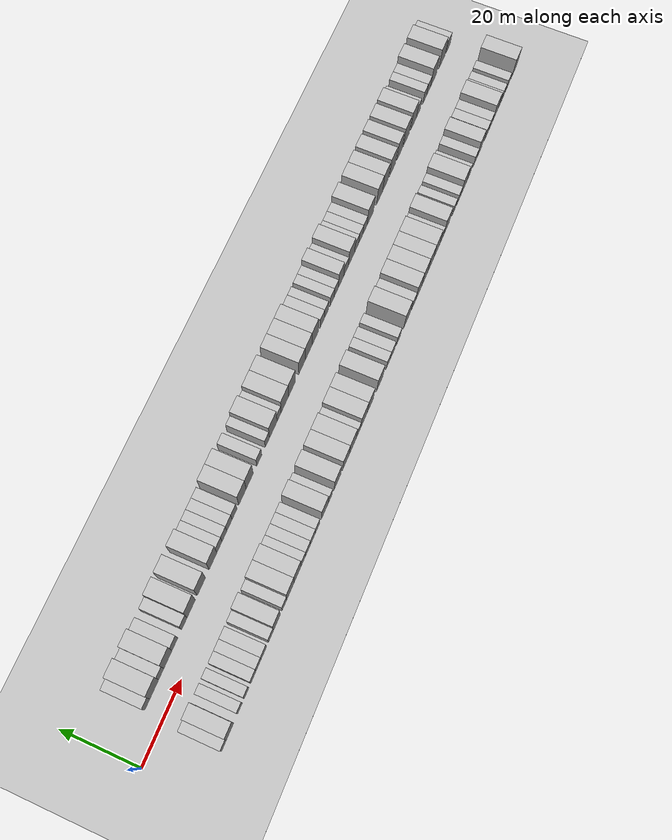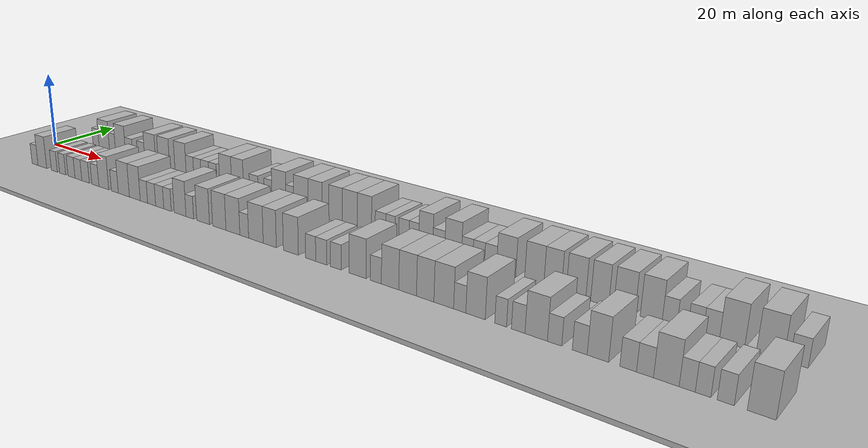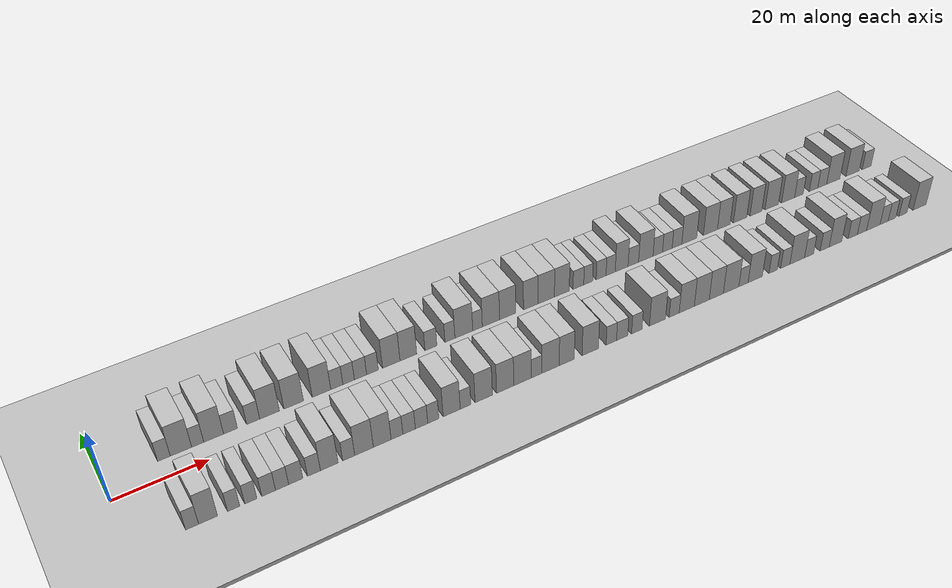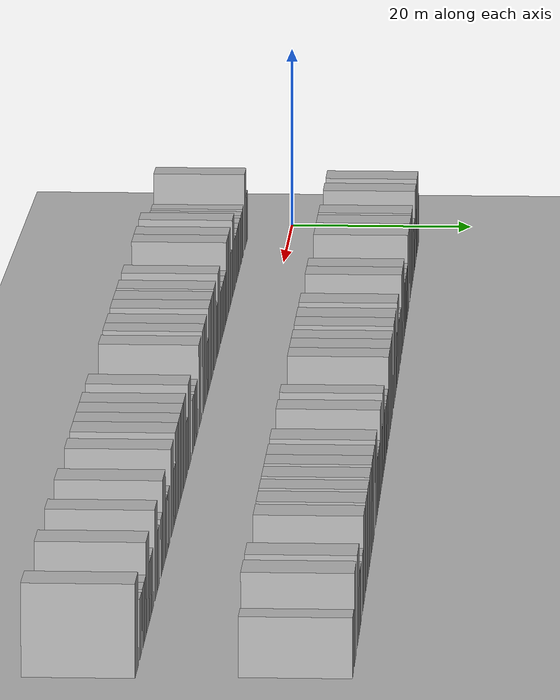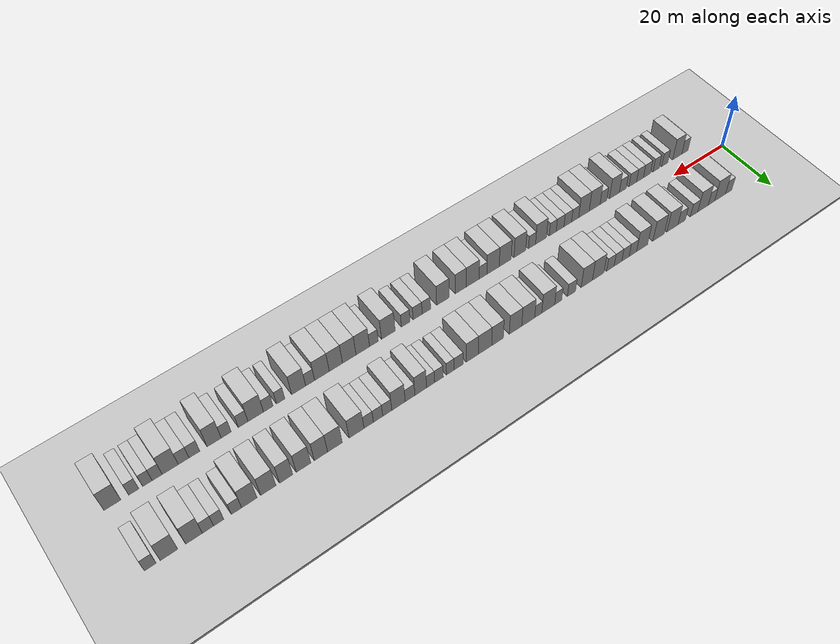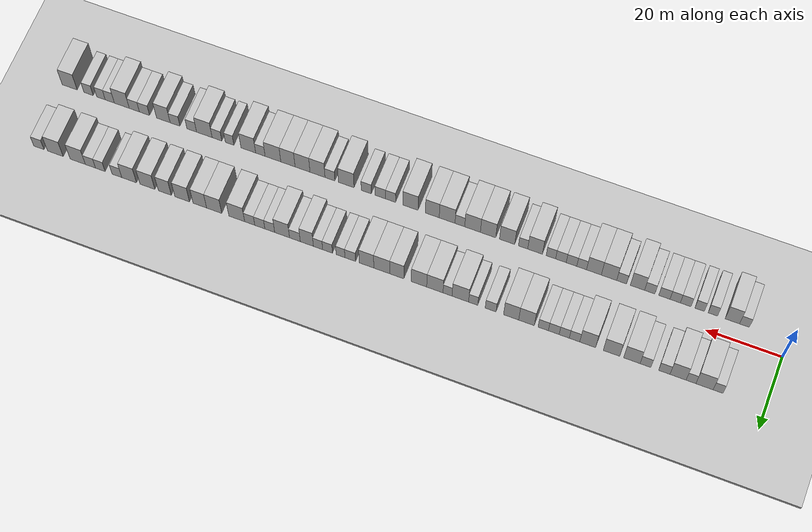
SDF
<?xml version="1.0" encoding="utf-8"?>

<sdf version="1.6">

   <world name="default">

      <gui fullscreen="0">

         <camera name="user_camera">

            <pose>-15 0 4.57585 0 0 0</pose>

            <view_controller>orbit</view_controller>

         </camera>

      </gui>

      <scene>

         <sky>

           <clouds>

             <speed>12</speed>

           </clouds>

         </sky>

         <ambient>0.4 0.4 0.4 1</ambient>

         <background>0.7 0.7 0.7 1</background>

         <shadows>1</shadows>

      </scene>

      <gravity>0 0 -9.8066</gravity>

      <magnetic_field>6e-06 2.3e-05 -4.2e-05</magnetic_field>

      <physics default="0" name="default_physics" type="ode">

         <ode>

            <solver>

               <type>quick</type>

               <iters>10</iters>

               <sor>1.0</sor>

               <use_dynamic_moi_rescaling>0</use_dynamic_moi_rescaling>

            </solver>

            <constraints>

               <cfm>0</cfm>

               <erp>0.2</erp>

               <contact_max_correcting_vel>100</contact_max_correcting_vel>

               <contact_surface_layer>0.001</contact_surface_layer>

            </constraints>

         </ode>

         <max_step_size>0.004</max_step_size>

         <real_time_factor>1</real_time_factor>

         <real_time_update_rate>250</real_time_update_rate>

      </physics>

      <light name="sun" type="directional">

         <cast_shadows>1</cast_shadows>

         <pose>0 0 10 0 0 0</pose>

         <diffuse>0.8 0.8 0.8 1</diffuse>

         <specular>0.2 0.2 0.2 1</specular>

         <attenuation>

            <range>1000</range>

            <constant>0.9</constant>

            <linear>0.01</linear>

            <quadratic>0.001</quadratic>

         </attenuation>

         <direction>-0.5 0.1 -0.9</direction>

      </light>

      <include>

         <name>ground_plane_1</name>

         <uri>model://HANNAS_ground_plane</uri>

         <pose>0 0 0  0 0 0</pose>

      </include>

      <include>

         <name>ground_plane_2</name>

         <uri>model://HANNAS_ground_plane</uri>

         <pose>100 0 0  0 0 0</pose>

      </include>

      <model name="building_1">

         <static>1</static>

         <pose frame="">12.2993 9.5000 0 0.000000 0.000000 1.570796</pose>

         <link name="link">

            <pose frame="">0 0 3.00 0 0 0</pose>

            <collision name="collision">

               <geometry>

                  <box>

                     <size>10.0000 2.5986 6.0000</size>

                  </box>

               </geometry>

               <max_contacts>10</max_contacts>

               <surface>

                  <contact>

                     <ode/>

                  </contact>

                  <bounce/>

                  <friction>

                     <torsional>

                        <ode/>

                     </torsional>

                     <ode/>

                  </friction>

               </surface>

            </collision>

            <visual name="visual">

               <cast_shadows>0</cast_shadows>

               <geometry>

                  <box>

                     <size>10.0000 2.5986 6.0000</size>

                  </box>

               </geometry>

               <material>

                  <script>

                     <uri>model://HANNAS_wall/materials/scripts</uri>

                     <uri>model://HANNAS_wall/materials/textures</uri>

                     <name>vrc/HANNAS_wall</name>

                  </script>

               </material>

            </visual>

            <self_collide>0</self_collide>

            <enable_wind>0</enable_wind>

            <kinematic>0</kinematic>

         </link>

      </model>

      <model name="building_2">

         <static>1</static>

         <pose frame="">15.8166 9.5000 0 0.000000 0.000000 1.570796</pose>

         <link name="link">

            <pose frame="">0 0 4.50 0 0 0</pose>

            <collision name="collision">

               <geometry>

                  <box>

                     <size>10.0000 4.4359 9.0000</size>

                  </box>

               </geometry>

               <max_contacts>10</max_contacts>

               <surface>

                  <contact>

                     <ode/>

                  </contact>

                  <bounce/>

                  <friction>

                     <torsional>

                        <ode/>

                     </torsional>

                     <ode/>

                  </friction>

               </surface>

            </collision>

            <visual name="visual">

               <cast_shadows>0</cast_shadows>

               <geometry>

                  <box>

                     <size>10.0000 4.4359 9.0000</size>

                  </box>

               </geometry>

               <material>

                  <script>

                     <uri>model://HANNAS_wall/materials/scripts</uri>

                     <uri>model://HANNAS_wall/materials/textures</uri>

                     <name>vrc/HANNAS_wall</name>

                  </script>

               </material>

            </visual>

            <self_collide>0</self_collide>

            <enable_wind>0</enable_wind>

            <kinematic>0</kinematic>

         </link>

      </model>

      <model name="building_3">

         <static>1</static>

         <pose frame="">19.3068 9.5000 0 0.000000 0.000000 1.570796</pose>

         <link name="link">

            <pose frame="">0 0 3.00 0 0 0</pose>

            <collision name="collision">

               <geometry>

                  <box>

                     <size>10.0000 2.5445 6.0000</size>

                  </box>

               </geometry>

               <max_contacts>10</max_contacts>

               <surface>

                  <contact>

                     <ode/>

                  </contact>

                  <bounce/>

                  <friction>

                     <torsional>

                        <ode/>

                     </torsional>

                     <ode/>

                  </friction>

               </surface>

            </collision>

            <visual name="visual">

               <cast_shadows>0</cast_shadows>

               <geometry>

                  <box>

                     <size>10.0000 2.5445 6.0000</size>

                  </box>

               </geometry>

               <material>

                  <script>

                     <uri>model://HANNAS_wall/materials/scripts</uri>

                     <uri>model://HANNAS_wall/materials/textures</uri>

                     <name>vrc/HANNAS_wall</name>

                  </script>

               </material>

            </visual>

            <self_collide>0</self_collide>

            <enable_wind>0</enable_wind>

            <kinematic>0</kinematic>

         </link>

      </model>

      <model name="building_4">

         <static>1</static>

         <pose frame="">22.6740 9.5000 0 0.000000 0.000000 1.570796</pose>

         <link name="link">

            <pose frame="">0 0 4.50 0 0 0</pose>

            <collision name="collision">

               <geometry>

                  <box>

                     <size>10.0000 4.1901 9.0000</size>

                  </box>

               </geometry>

               <max_contacts>10</max_contacts>

               <surface>

                  <contact>

                     <ode/>

                  </contact>

                  <bounce/>

                  <friction>

                     <torsional>

                        <ode/>

                     </torsional>

                     <ode/>

                  </friction>

               </surface>

            </collision>

            <visual name="visual">

               <cast_shadows>0</cast_shadows>

               <geometry>

                  <box>

                     <size>10.0000 4.1901 9.0000</size>

                  </box>

               </geometry>

               <material>

                  <script>

                     <uri>model://HANNAS_wall/materials/scripts</uri>

                     <uri>model://HANNAS_wall/materials/textures</uri>

                     <name>vrc/HANNAS_wall</name>

                  </script>

               </material>

            </visual>

            <self_collide>0</self_collide>

            <enable_wind>0</enable_wind>

            <kinematic>0</kinematic>

         </link>

      </model>

      <model name="building_5">

         <static>1</static>

         <pose frame="">26.2498 9.5000 0 0.000000 0.000000 1.570796</pose>

         <link name="link">

            <pose frame="">0 0 3.00 0 0 0</pose>

            <collision name="collision">

               <geometry>

                  <box>

                     <size>10.0000 2.9615 6.0000</size>

                  </box>

               </geometry>

               <max_contacts>10</max_contacts>

               <surface>

                  <contact>

                     <ode/>

                  </contact>

                  <bounce/>

                  <friction>

                     <torsional>

                        <ode/>

                     </torsional>

                     <ode/>

                  </friction>

               </surface>

            </collision>

            <visual name="visual">

               <cast_shadows>0</cast_shadows>

               <geometry>

                  <box>

                     <size>10.0000 2.9615 6.0000</size>

                  </box>

               </geometry>

               <material>

                  <script>

                     <uri>model://HANNAS_wall/materials/scripts</uri>

                     <uri>model://HANNAS_wall/materials/textures</uri>

                     <name>vrc/HANNAS_wall</name>

                  </script>

               </material>

            </visual>

            <self_collide>0</self_collide>

            <enable_wind>0</enable_wind>

            <kinematic>0</kinematic>

         </link>

      </model>

      <model name="building_6">

         <static>1</static>

         <pose frame="">31.1484 9.5000 0 0.000000 0.000000 1.570796</pose>

         <link name="link">

            <pose frame="">0 0 3.00 0 0 0</pose>

            <collision name="collision">

               <geometry>

                  <box>

                     <size>10.0000 2.8357 6.0000</size>

                  </box>

               </geometry>

               <max_contacts>10</max_contacts>

               <surface>

                  <contact>

                     <ode/>

                  </contact>

                  <bounce/>

                  <friction>

                     <torsional>

                        <ode/>

                     </torsional>

                     <ode/>

                  </friction>

               </surface>

            </collision>

            <visual name="visual">

               <cast_shadows>0</cast_shadows>

               <geometry>

                  <box>

                     <size>10.0000 2.8357 6.0000</size>

                  </box>

               </geometry>

               <material>

                  <script>

                     <uri>model://HANNAS_wall/materials/scripts</uri>

                     <uri>model://HANNAS_wall/materials/textures</uri>

                     <name>vrc/HANNAS_wall</name>

                  </script>

               </material>

            </visual>

            <self_collide>0</self_collide>

            <enable_wind>0</enable_wind>

            <kinematic>0</kinematic>

         </link>

      </model>

      <model name="building_7">

         <static>1</static>

         <pose frame="">34.7326 9.5000 0 0.000000 0.000000 1.570796</pose>

         <link name="link">

            <pose frame="">0 0 4.50 0 0 0</pose>

            <collision name="collision">

               <geometry>

                  <box>

                     <size>10.0000 4.3327 9.0000</size>

                  </box>

               </geometry>

               <max_contacts>10</max_contacts>

               <surface>

                  <contact>

                     <ode/>

                  </contact>

                  <bounce/>

                  <friction>

                     <torsional>

                        <ode/>

                     </torsional>

                     <ode/>

                  </friction>

               </surface>

            </collision>

            <visual name="visual">

               <cast_shadows>0</cast_shadows>

               <geometry>

                  <box>

                     <size>10.0000 4.3327 9.0000</size>

                  </box>

               </geometry>

               <material>

                  <script>

                     <uri>model://HANNAS_wall/materials/scripts</uri>

                     <uri>model://HANNAS_wall/materials/textures</uri>

                     <name>vrc/HANNAS_wall</name>

                  </script>

               </material>

            </visual>

            <self_collide>0</self_collide>

            <enable_wind>0</enable_wind>

            <kinematic>0</kinematic>

         </link>

      </model>

      <model name="building_8">

         <static>1</static>

         <pose frame="">40.0762 9.5000 0 0.000000 0.000000 1.570796</pose>

         <link name="link">

            <pose frame="">0 0 4.50 0 0 0</pose>

            <collision name="collision">

               <geometry>

                  <box>

                     <size>10.0000 4.3544 9.0000</size>

                  </box>

               </geometry>

               <max_contacts>10</max_contacts>

               <surface>

                  <contact>

                     <ode/>

                  </contact>

                  <bounce/>

                  <friction>

                     <torsional>

                        <ode/>

                     </torsional>

                     <ode/>

                  </friction>

               </surface>

            </collision>

            <visual name="visual">

               <cast_shadows>0</cast_shadows>

               <geometry>

                  <box>

                     <size>10.0000 4.3544 9.0000</size>

                  </box>

               </geometry>

               <material>

                  <script>

                     <uri>model://HANNAS_wall/materials/scripts</uri>

                     <uri>model://HANNAS_wall/materials/textures</uri>

                     <name>vrc/HANNAS_wall</name>

                  </script>

               </material>

            </visual>

            <self_collide>0</self_collide>

            <enable_wind>0</enable_wind>

            <kinematic>0</kinematic>

         </link>

      </model>

      <model name="building_9">

         <static>1</static>

         <pose frame="">46.3475 9.5000 0 0.000000 0.000000 1.570796</pose>

         <link name="link">

            <pose frame="">0 0 4.50 0 0 0</pose>

            <collision name="collision">

               <geometry>

                  <box>

                     <size>10.0000 4.1883 9.0000</size>

                  </box>

               </geometry>

               <max_contacts>10</max_contacts>

               <surface>

                  <contact>

                     <ode/>

                  </contact>

                  <bounce/>

                  <friction>

                     <torsional>

                        <ode/>

                     </torsional>

                     <ode/>

                  </friction>

               </surface>

            </collision>

            <visual name="visual">

               <cast_shadows>0</cast_shadows>

               <geometry>

                  <box>

                     <size>10.0000 4.1883 9.0000</size>

                  </box>

               </geometry>

               <material>

                  <script>

                     <uri>model://HANNAS_wall/materials/scripts</uri>

                     <uri>model://HANNAS_wall/materials/textures</uri>

                     <name>vrc/HANNAS_wall</name>

                  </script>

               </material>

            </visual>

            <self_collide>0</self_collide>

            <enable_wind>0</enable_wind>

            <kinematic>0</kinematic>

         </link>

      </model>

      <model name="building_10">

         <static>1</static>

         <pose frame="">49.8299 9.5000 0 0.000000 0.000000 1.570796</pose>

         <link name="link">

            <pose frame="">0 0 3.00 0 0 0</pose>

            <collision name="collision">

               <geometry>

                  <box>

                     <size>10.0000 2.7763 6.0000</size>

                  </box>

               </geometry>

               <max_contacts>10</max_contacts>

               <surface>

                  <contact>

                     <ode/>

                  </contact>

                  <bounce/>

                  <friction>

                     <torsional>

                        <ode/>

                     </torsional>

                     <ode/>

                  </friction>

               </surface>

            </collision>

            <visual name="visual">

               <cast_shadows>0</cast_shadows>

               <geometry>

                  <box>

                     <size>10.0000 2.7763 6.0000</size>

                  </box>

               </geometry>

               <material>

                  <script>

                     <uri>model://HANNAS_wall/materials/scripts</uri>

                     <uri>model://HANNAS_wall/materials/textures</uri>

                     <name>vrc/HANNAS_wall</name>

                  </script>

               </material>

            </visual>

            <self_collide>0</self_collide>

            <enable_wind>0</enable_wind>

            <kinematic>0</kinematic>

         </link>

      </model>

      <model name="building_11">

         <static>1</static>

         <pose frame="">52.5559 9.5000 0 0.000000 0.000000 1.570796</pose>

         <link name="link">

            <pose frame="">0 0 3.00 0 0 0</pose>

            <collision name="collision">

               <geometry>

                  <box>

                     <size>10.0000 2.6757 6.0000</size>

                  </box>

               </geometry>

               <max_contacts>10</max_contacts>

               <surface>

                  <contact>

                     <ode/>

                  </contact>

                  <bounce/>

                  <friction>

                     <torsional>

                        <ode/>

                     </torsional>

                     <ode/>

                  </friction>

               </surface>

            </collision>

            <visual name="visual">

               <cast_shadows>0</cast_shadows>

               <geometry>

                  <box>

                     <size>10.0000 2.6757 6.0000</size>

                  </box>

               </geometry>

               <material>

                  <script>

                     <uri>model://HANNAS_wall/materials/scripts</uri>

                     <uri>model://HANNAS_wall/materials/textures</uri>

                     <name>vrc/HANNAS_wall</name>

                  </script>

               </material>

            </visual>

            <self_collide>0</self_collide>

            <enable_wind>0</enable_wind>

            <kinematic>0</kinematic>

         </link>

      </model>

      <model name="building_12">

         <static>1</static>

         <pose frame="">55.3262 9.5000 0 0.000000 0.000000 1.570796</pose>

         <link name="link">

            <pose frame="">0 0 3.00 0 0 0</pose>

            <collision name="collision">

               <geometry>

                  <box>

                     <size>10.0000 2.8649 6.0000</size>

                  </box>

               </geometry>

               <max_contacts>10</max_contacts>

               <surface>

                  <contact>

                     <ode/>

                  </contact>

                  <bounce/>

                  <friction>

                     <torsional>

                        <ode/>

                     </torsional>

                     <ode/>

                  </friction>

               </surface>

            </collision>

            <visual name="visual">

               <cast_shadows>0</cast_shadows>

               <geometry>

                  <box>

                     <size>10.0000 2.8649 6.0000</size>

                  </box>

               </geometry>

               <material>

                  <script>

                     <uri>model://HANNAS_wall/materials/scripts</uri>

                     <uri>model://HANNAS_wall/materials/textures</uri>

                     <name>vrc/HANNAS_wall</name>

                  </script>

               </material>

            </visual>

            <self_collide>0</self_collide>

            <enable_wind>0</enable_wind>

            <kinematic>0</kinematic>

         </link>

      </model>

      <model name="building_13">

         <static>1</static>

         <pose frame="">58.1274 9.5000 0 0.000000 0.000000 1.570796</pose>

         <link name="link">

            <pose frame="">0 0 3.00 0 0 0</pose>

            <collision name="collision">

               <geometry>

                  <box>

                     <size>10.0000 2.7375 6.0000</size>

                  </box>

               </geometry>

               <max_contacts>10</max_contacts>

               <surface>

                  <contact>

                     <ode/>

                  </contact>

                  <bounce/>

                  <friction>

                     <torsional>

                        <ode/>

                     </torsional>

                     <ode/>

                  </friction>

               </surface>

            </collision>

            <visual name="visual">

               <cast_shadows>0</cast_shadows>

               <geometry>

                  <box>

                     <size>10.0000 2.7375 6.0000</size>

                  </box>

               </geometry>

               <material>

                  <script>

                     <uri>model://HANNAS_wall/materials/scripts</uri>

                     <uri>model://HANNAS_wall/materials/textures</uri>

                     <name>vrc/HANNAS_wall</name>

                  </script>

               </material>

            </visual>

            <self_collide>0</self_collide>

            <enable_wind>0</enable_wind>

            <kinematic>0</kinematic>

         </link>

      </model>

      <model name="building_14">

         <static>1</static>

         <pose frame="">62.5772 9.5000 0 0.000000 0.000000 1.570796</pose>

         <link name="link">

            <pose frame="">0 0 4.50 0 0 0</pose>

            <collision name="collision">

               <geometry>

                  <box>

                     <size>10.0000 4.1623 9.0000</size>

                  </box>

               </geometry>

               <max_contacts>10</max_contacts>

               <surface>

                  <contact>

                     <ode/>

                  </contact>

                  <bounce/>

                  <friction>

                     <torsional>

                        <ode/>

                     </torsional>

                     <ode/>

                  </friction>

               </surface>

            </collision>

            <visual name="visual">

               <cast_shadows>0</cast_shadows>

               <geometry>

                  <box>

                     <size>10.0000 4.1623 9.0000</size>

                  </box>

               </geometry>

               <material>

                  <script>

                     <uri>model://HANNAS_wall/materials/scripts</uri>

                     <uri>model://HANNAS_wall/materials/textures</uri>

                     <name>vrc/HANNAS_wall</name>

                  </script>

               </material>

            </visual>

            <self_collide>0</self_collide>

            <enable_wind>0</enable_wind>

            <kinematic>0</kinematic>

         </link>

      </model>

      <model name="building_15">

         <static>1</static>

         <pose frame="">66.6766 9.5000 0 0.000000 0.000000 1.570796</pose>

         <link name="link">

            <pose frame="">0 0 4.50 0 0 0</pose>

            <collision name="collision">

               <geometry>

                  <box>

                     <size>10.0000 4.0365 9.0000</size>

                  </box>

               </geometry>

               <max_contacts>10</max_contacts>

               <surface>

                  <contact>

                     <ode/>

                  </contact>

                  <bounce/>

                  <friction>

                     <torsional>

                        <ode/>

                     </torsional>

                     <ode/>

                  </friction>

               </surface>

            </collision>

            <visual name="visual">

               <cast_shadows>0</cast_shadows>

               <geometry>

                  <box>

                     <size>10.0000 4.0365 9.0000</size>

                  </box>

               </geometry>

               <material>

                  <script>

                     <uri>model://HANNAS_wall/materials/scripts</uri>

                     <uri>model://HANNAS_wall/materials/textures</uri>

                     <name>vrc/HANNAS_wall</name>

                  </script>

               </material>

            </visual>

            <self_collide>0</self_collide>

            <enable_wind>0</enable_wind>

            <kinematic>0</kinematic>

         </link>

      </model>

      <model name="building_16">

         <static>1</static>

         <pose frame="">72.1498 9.5000 0 0.000000 0.000000 1.570796</pose>

         <link name="link">

            <pose frame="">0 0 3.00 0 0 0</pose>

            <collision name="collision">

               <geometry>

                  <box>

                     <size>10.0000 2.9097 6.0000</size>

                  </box>

               </geometry>

               <max_contacts>10</max_contacts>

               <surface>

                  <contact>

                     <ode/>

                  </contact>

                  <bounce/>

                  <friction>

                     <torsional>

                        <ode/>

                     </torsional>

                     <ode/>

                  </friction>

               </surface>

            </collision>

            <visual name="visual">

               <cast_shadows>0</cast_shadows>

               <geometry>

                  <box>

                     <size>10.0000 2.9097 6.0000</size>

                  </box>

               </geometry>

               <material>

                  <script>

                     <uri>model://HANNAS_wall/materials/scripts</uri>

                     <uri>model://HANNAS_wall/materials/textures</uri>

                     <name>vrc/HANNAS_wall</name>

                  </script>

               </material>

            </visual>

            <self_collide>0</self_collide>

            <enable_wind>0</enable_wind>

            <kinematic>0</kinematic>

         </link>

      </model>

      <model name="building_17">

         <static>1</static>

         <pose frame="">76.8367 9.5000 0 0.000000 0.000000 1.570796</pose>

         <link name="link">

            <pose frame="">0 0 3.00 0 0 0</pose>

            <collision name="collision">

               <geometry>

                  <box>

                     <size>10.0000 2.4643 6.0000</size>

                  </box>

               </geometry>

               <max_contacts>10</max_contacts>

               <surface>

                  <contact>

                     <ode/>

                  </contact>

                  <bounce/>

                  <friction>

                     <torsional>

                        <ode/>

                     </torsional>

                     <ode/>

                  </friction>

               </surface>

            </collision>

            <visual name="visual">

               <cast_shadows>0</cast_shadows>

               <geometry>

                  <box>

                     <size>10.0000 2.4643 6.0000</size>

                  </box>

               </geometry>

               <material>

                  <script>

                     <uri>model://HANNAS_wall/materials/scripts</uri>

                     <uri>model://HANNAS_wall/materials/textures</uri>

                     <name>vrc/HANNAS_wall</name>

                  </script>

               </material>

            </visual>

            <self_collide>0</self_collide>

            <enable_wind>0</enable_wind>

            <kinematic>0</kinematic>

         </link>

      </model>

      <model name="building_18">

         <static>1</static>

         <pose frame="">80.3008 9.5000 0 0.000000 0.000000 1.570796</pose>

         <link name="link">

            <pose frame="">0 0 4.50 0 0 0</pose>

            <collision name="collision">

               <geometry>

                  <box>

                     <size>10.0000 4.4638 9.0000</size>

                  </box>

               </geometry>

               <max_contacts>10</max_contacts>

               <surface>

                  <contact>

                     <ode/>

                  </contact>

                  <bounce/>

                  <friction>

                     <torsional>

                        <ode/>

                     </torsional>

                     <ode/>

                  </friction>

               </surface>

            </collision>

            <visual name="visual">

               <cast_shadows>0</cast_shadows>

               <geometry>

                  <box>

                     <size>10.0000 4.4638 9.0000</size>

                  </box>

               </geometry>

               <material>

                  <script>

                     <uri>model://HANNAS_wall/materials/scripts</uri>

                     <uri>model://HANNAS_wall/materials/textures</uri>

                     <name>vrc/HANNAS_wall</name>

                  </script>

               </material>

            </visual>

            <self_collide>0</self_collide>

            <enable_wind>0</enable_wind>

            <kinematic>0</kinematic>

         </link>

      </model>

      <model name="building_19">

         <static>1</static>

         <pose frame="">83.7468 9.5000 0 0.000000 0.000000 1.570796</pose>

         <link name="link">

            <pose frame="">0 0 3.00 0 0 0</pose>

            <collision name="collision">

               <geometry>

                  <box>

                     <size>10.0000 2.4282 6.0000</size>

                  </box>

               </geometry>

               <max_contacts>10</max_contacts>

               <surface>

                  <contact>

                     <ode/>

                  </contact>

                  <bounce/>

                  <friction>

                     <torsional>

                        <ode/>

                     </torsional>

                     <ode/>

                  </friction>

               </surface>

            </collision>

            <visual name="visual">

               <cast_shadows>0</cast_shadows>

               <geometry>

                  <box>

                     <size>10.0000 2.4282 6.0000</size>

                  </box>

               </geometry>

               <material>

                  <script>

                     <uri>model://HANNAS_wall/materials/scripts</uri>

                     <uri>model://HANNAS_wall/materials/textures</uri>

                     <name>vrc/HANNAS_wall</name>

                  </script>

               </material>

            </visual>

            <self_collide>0</self_collide>

            <enable_wind>0</enable_wind>

            <kinematic>0</kinematic>

         </link>

      </model>

      <model name="building_20">

         <static>1</static>

         <pose frame="">87.1645 9.5000 0 0.000000 0.000000 1.570796</pose>

         <link name="link">

            <pose frame="">0 0 4.50 0 0 0</pose>

            <collision name="collision">

               <geometry>

                  <box>

                     <size>10.0000 4.4072 9.0000</size>

                  </box>

               </geometry>

               <max_contacts>10</max_contacts>

               <surface>

                  <contact>

                     <ode/>

                  </contact>

                  <bounce/>

                  <friction>

                     <torsional>

                        <ode/>

                     </torsional>

                     <ode/>

                  </friction>

               </surface>

            </collision>

            <visual name="visual">

               <cast_shadows>0</cast_shadows>

               <geometry>

                  <box>

                     <size>10.0000 4.4072 9.0000</size>

                  </box>

               </geometry>

               <material>

                  <script>

                     <uri>model://HANNAS_wall/materials/scripts</uri>

                     <uri>model://HANNAS_wall/materials/textures</uri>

                     <name>vrc/HANNAS_wall</name>

                  </script>

               </material>

            </visual>

            <self_collide>0</self_collide>

            <enable_wind>0</enable_wind>

            <kinematic>0</kinematic>

         </link>

      </model>

      <model name="building_21">

         <static>1</static>

         <pose frame="">91.4598 9.5000 0 0.000000 0.000000 1.570796</pose>

         <link name="link">

            <pose frame="">0 0 4.50 0 0 0</pose>

            <collision name="collision">

               <geometry>

                  <box>

                     <size>10.0000 4.1834 9.0000</size>

                  </box>

               </geometry>

               <max_contacts>10</max_contacts>

               <surface>

                  <contact>

                     <ode/>

                  </contact>

                  <bounce/>

                  <friction>

                     <torsional>

                        <ode/>

                     </torsional>

                     <ode/>

                  </friction>

               </surface>

            </collision>

            <visual name="visual">

               <cast_shadows>0</cast_shadows>

               <geometry>

                  <box>

                     <size>10.0000 4.1834 9.0000</size>

                  </box>

               </geometry>

               <material>

                  <script>

                     <uri>model://HANNAS_wall/materials/scripts</uri>

                     <uri>model://HANNAS_wall/materials/textures</uri>

                     <name>vrc/HANNAS_wall</name>

                  </script>

               </material>

            </visual>

            <self_collide>0</self_collide>

            <enable_wind>0</enable_wind>

            <kinematic>0</kinematic>

         </link>

      </model>

      <model name="building_22">

         <static>1</static>

         <pose frame="">97.4769 9.5000 0 0.000000 0.000000 1.570796</pose>

         <link name="link">

            <pose frame="">0 0 4.50 0 0 0</pose>

            <collision name="collision">

               <geometry>

                  <box>

                     <size>10.0000 3.8507 9.0000</size>

                  </box>

               </geometry>

               <max_contacts>10</max_contacts>

               <surface>

                  <contact>

                     <ode/>

                  </contact>

                  <bounce/>

                  <friction>

                     <torsional>

                        <ode/>

                     </torsional>

                     <ode/>

                  </friction>

               </surface>

            </collision>

            <visual name="visual">

               <cast_shadows>0</cast_shadows>

               <geometry>

                  <box>

                     <size>10.0000 3.8507 9.0000</size>

                  </box>

               </geometry>

               <material>

                  <script>

                     <uri>model://HANNAS_wall/materials/scripts</uri>

                     <uri>model://HANNAS_wall/materials/textures</uri>

                     <name>vrc/HANNAS_wall</name>

                  </script>

               </material>

            </visual>

            <self_collide>0</self_collide>

            <enable_wind>0</enable_wind>

            <kinematic>0</kinematic>

         </link>

      </model>

      <model name="building_23">

         <static>1</static>

         <pose frame="">101.5663 9.5000 0 0.000000 0.000000 1.570796</pose>

         <link name="link">

            <pose frame="">0 0 4.50 0 0 0</pose>

            <collision name="collision">

               <geometry>

                  <box>

                     <size>10.0000 4.3280 9.0000</size>

                  </box>

               </geometry>

               <max_contacts>10</max_contacts>

               <surface>

                  <contact>

                     <ode/>

                  </contact>

                  <bounce/>

                  <friction>

                     <torsional>

                        <ode/>

                     </torsional>

                     <ode/>

                  </friction>

               </surface>

            </collision>

            <visual name="visual">

               <cast_shadows>0</cast_shadows>

               <geometry>

                  <box>

                     <size>10.0000 4.3280 9.0000</size>

                  </box>

               </geometry>

               <material>

                  <script>

                     <uri>model://HANNAS_wall/materials/scripts</uri>

                     <uri>model://HANNAS_wall/materials/textures</uri>

                     <name>vrc/HANNAS_wall</name>

                  </script>

               </material>

            </visual>

            <self_collide>0</self_collide>

            <enable_wind>0</enable_wind>

            <kinematic>0</kinematic>

         </link>

      </model>

      <model name="building_24">

         <static>1</static>

         <pose frame="">105.7196 9.5000 0 0.000000 0.000000 1.570796</pose>

         <link name="link">

            <pose frame="">0 0 4.50 0 0 0</pose>

            <collision name="collision">

               <geometry>

                  <box>

                     <size>10.0000 3.9787 9.0000</size>

                  </box>

               </geometry>

               <max_contacts>10</max_contacts>

               <surface>

                  <contact>

                     <ode/>

                  </contact>

                  <bounce/>

                  <friction>

                     <torsional>

                        <ode/>

                     </torsional>

                     <ode/>

                  </friction>

               </surface>

            </collision>

            <visual name="visual">

               <cast_shadows>0</cast_shadows>

               <geometry>

                  <box>

                     <size>10.0000 3.9787 9.0000</size>

                  </box>

               </geometry>

               <material>

                  <script>

                     <uri>model://HANNAS_wall/materials/scripts</uri>

                     <uri>model://HANNAS_wall/materials/textures</uri>

                     <name>vrc/HANNAS_wall</name>

                  </script>

               </material>

            </visual>

            <self_collide>0</self_collide>

            <enable_wind>0</enable_wind>

            <kinematic>0</kinematic>

         </link>

      </model>

      <model name="building_25">

         <static>1</static>

         <pose frame="">110.1704 9.5000 0 0.000000 0.000000 1.570796</pose>

         <link name="link">

            <pose frame="">0 0 3.00 0 0 0</pose>

            <collision name="collision">

               <geometry>

                  <box>

                     <size>10.0000 2.9229 6.0000</size>

                  </box>

               </geometry>

               <max_contacts>10</max_contacts>

               <surface>

                  <contact>

                     <ode/>

                  </contact>

                  <bounce/>

                  <friction>

                     <torsional>

                        <ode/>

                     </torsional>

                     <ode/>

                  </friction>

               </surface>

            </collision>

            <visual name="visual">

               <cast_shadows>0</cast_shadows>

               <geometry>

                  <box>

                     <size>10.0000 2.9229 6.0000</size>

                  </box>

               </geometry>

               <material>

                  <script>

                     <uri>model://HANNAS_wall/materials/scripts</uri>

                     <uri>model://HANNAS_wall/materials/textures</uri>

                     <name>vrc/HANNAS_wall</name>

                  </script>

               </material>

            </visual>

            <self_collide>0</self_collide>

            <enable_wind>0</enable_wind>

            <kinematic>0</kinematic>

         </link>

      </model>

      <model name="building_26">

         <static>1</static>

         <pose frame="">112.8469 9.5000 0 0.000000 0.000000 1.570796</pose>

         <link name="link">

            <pose frame="">0 0 3.00 0 0 0</pose>

            <collision name="collision">

               <geometry>

                  <box>

                     <size>10.0000 2.4302 6.0000</size>

                  </box>

               </geometry>

               <max_contacts>10</max_contacts>

               <surface>

                  <contact>

                     <ode/>

                  </contact>

                  <bounce/>

                  <friction>

                     <torsional>

                        <ode/>

                     </torsional>

                     <ode/>

                  </friction>

               </surface>

            </collision>

            <visual name="visual">

               <cast_shadows>0</cast_shadows>

               <geometry>

                  <box>

                     <size>10.0000 2.4302 6.0000</size>

                  </box>

               </geometry>

               <material>

                  <script>

                     <uri>model://HANNAS_wall/materials/scripts</uri>

                     <uri>model://HANNAS_wall/materials/textures</uri>

                     <name>vrc/HANNAS_wall</name>

                  </script>

               </material>

            </visual>

            <self_collide>0</self_collide>

            <enable_wind>0</enable_wind>

            <kinematic>0</kinematic>

         </link>

      </model>

      <model name="building_27">

         <static>1</static>

         <pose frame="">116.4080 9.5000 0 0.000000 0.000000 1.570796</pose>

         <link name="link">

            <pose frame="">0 0 3.00 0 0 0</pose>

            <collision name="collision">

               <geometry>

                  <box>

                     <size>10.0000 2.6919 6.0000</size>

                  </box>

               </geometry>

               <max_contacts>10</max_contacts>

               <surface>

                  <contact>

                     <ode/>

                  </contact>

                  <bounce/>

                  <friction>

                     <torsional>

                        <ode/>

                     </torsional>

                     <ode/>

                  </friction>

               </surface>

            </collision>

            <visual name="visual">

               <cast_shadows>0</cast_shadows>

               <geometry>

                  <box>

                     <size>10.0000 2.6919 6.0000</size>

                  </box>

               </geometry>

               <material>

                  <script>

                     <uri>model://HANNAS_wall/materials/scripts</uri>

                     <uri>model://HANNAS_wall/materials/textures</uri>

                     <name>vrc/HANNAS_wall</name>

                  </script>

               </material>

            </visual>

            <self_collide>0</self_collide>

            <enable_wind>0</enable_wind>

            <kinematic>0</kinematic>

         </link>

      </model>

      <model name="building_28">

         <static>1</static>

         <pose frame="">119.0302 9.5000 0 0.000000 0.000000 1.570796</pose>

         <link name="link">

            <pose frame="">0 0 3.00 0 0 0</pose>

            <collision name="collision">

               <geometry>

                  <box>

                     <size>10.0000 2.5525 6.0000</size>

                  </box>

               </geometry>

               <max_contacts>10</max_contacts>

               <surface>

                  <contact>

                     <ode/>

                  </contact>

                  <bounce/>

                  <friction>

                     <torsional>

                        <ode/>

                     </torsional>

                     <ode/>

                  </friction>

               </surface>

            </collision>

            <visual name="visual">

               <cast_shadows>0</cast_shadows>

               <geometry>

                  <box>

                     <size>10.0000 2.5525 6.0000</size>

                  </box>

               </geometry>

               <material>

                  <script>

                     <uri>model://HANNAS_wall/materials/scripts</uri>

                     <uri>model://HANNAS_wall/materials/textures</uri>

                     <name>vrc/HANNAS_wall</name>

                  </script>

               </material>

            </visual>

            <self_collide>0</self_collide>

            <enable_wind>0</enable_wind>

            <kinematic>0</kinematic>

         </link>

      </model>

      <model name="building_29">

         <static>1</static>

         <pose frame="">122.1112 9.5000 0 0.000000 0.000000 1.570796</pose>

         <link name="link">

            <pose frame="">0 0 4.50 0 0 0</pose>

            <collision name="collision">

               <geometry>

                  <box>

                     <size>10.0000 3.6096 9.0000</size>

                  </box>

               </geometry>

               <max_contacts>10</max_contacts>

               <surface>

                  <contact>

                     <ode/>

                  </contact>

                  <bounce/>

                  <friction>

                     <torsional>

                        <ode/>

                     </torsional>

                     <ode/>

                  </friction>

               </surface>

            </collision>

            <visual name="visual">

               <cast_shadows>0</cast_shadows>

               <geometry>

                  <box>

                     <size>10.0000 3.6096 9.0000</size>

                  </box>

               </geometry>

               <material>

                  <script>

                     <uri>model://HANNAS_wall/materials/scripts</uri>

                     <uri>model://HANNAS_wall/materials/textures</uri>

                     <name>vrc/HANNAS_wall</name>

                  </script>

               </material>

            </visual>

            <self_collide>0</self_collide>

            <enable_wind>0</enable_wind>

            <kinematic>0</kinematic>

         </link>

      </model>

      <model name="building_30">

         <static>1</static>

         <pose frame="">125.4067 9.5000 0 0.000000 0.000000 1.570796</pose>

         <link name="link">

            <pose frame="">0 0 3.00 0 0 0</pose>

            <collision name="collision">

               <geometry>

                  <box>

                     <size>10.0000 2.9814 6.0000</size>

                  </box>

               </geometry>

               <max_contacts>10</max_contacts>

               <surface>

                  <contact>

                     <ode/>

                  </contact>

                  <bounce/>

                  <friction>

                     <torsional>

                        <ode/>

                     </torsional>

                     <ode/>

                  </friction>

               </surface>

            </collision>

            <visual name="visual">

               <cast_shadows>0</cast_shadows>

               <geometry>

                  <box>

                     <size>10.0000 2.9814 6.0000</size>

                  </box>

               </geometry>

               <material>

                  <script>

                     <uri>model://HANNAS_wall/materials/scripts</uri>

                     <uri>model://HANNAS_wall/materials/textures</uri>

                     <name>vrc/HANNAS_wall</name>

                  </script>

               </material>

            </visual>

            <self_collide>0</self_collide>

            <enable_wind>0</enable_wind>

            <kinematic>0</kinematic>

         </link>

      </model>

      <model name="building_31">

         <static>1</static>

         <pose frame="">128.9537 9.5000 0 0.000000 0.000000 1.570796</pose>

         <link name="link">

            <pose frame="">0 0 4.50 0 0 0</pose>

            <collision name="collision">

               <geometry>

                  <box>

                     <size>10.0000 4.1126 9.0000</size>

                  </box>

               </geometry>

               <max_contacts>10</max_contacts>

               <surface>

                  <contact>

                     <ode/>

                  </contact>

                  <bounce/>

                  <friction>

                     <torsional>

                        <ode/>

                     </torsional>

                     <ode/>

                  </friction>

               </surface>

            </collision>

            <visual name="visual">

               <cast_shadows>0</cast_shadows>

               <geometry>

                  <box>

                     <size>10.0000 4.1126 9.0000</size>

                  </box>

               </geometry>

               <material>

                  <script>

                     <uri>model://HANNAS_wall/materials/scripts</uri>

                     <uri>model://HANNAS_wall/materials/textures</uri>

                     <name>vrc/HANNAS_wall</name>

                  </script>

               </material>

            </visual>

            <self_collide>0</self_collide>

            <enable_wind>0</enable_wind>

            <kinematic>0</kinematic>

         </link>

      </model>

      <model name="building_32">

         <static>1</static>

         <pose frame="">132.3761 9.5000 0 0.000000 0.000000 1.570796</pose>

         <link name="link">

            <pose frame="">0 0 3.00 0 0 0</pose>

            <collision name="collision">

               <geometry>

                  <box>

                     <size>10.0000 2.7322 6.0000</size>

                  </box>

               </geometry>

               <max_contacts>10</max_contacts>

               <surface>

                  <contact>

                     <ode/>

                  </contact>

                  <bounce/>

                  <friction>

                     <torsional>

                        <ode/>

                     </torsional>

                     <ode/>

                  </friction>

               </surface>

            </collision>

            <visual name="visual">

               <cast_shadows>0</cast_shadows>

               <geometry>

                  <box>

                     <size>10.0000 2.7322 6.0000</size>

                  </box>

               </geometry>

               <material>

                  <script>

                     <uri>model://HANNAS_wall/materials/scripts</uri>

                     <uri>model://HANNAS_wall/materials/textures</uri>

                     <name>vrc/HANNAS_wall</name>

                  </script>

               </material>

            </visual>

            <self_collide>0</self_collide>

            <enable_wind>0</enable_wind>

            <kinematic>0</kinematic>

         </link>

      </model>

      <model name="building_33">

         <static>1</static>

         <pose frame="">135.1400 9.5000 0 0.000000 0.000000 1.570796</pose>

         <link name="link">

            <pose frame="">0 0 3.00 0 0 0</pose>

            <collision name="collision">

               <geometry>

                  <box>

                     <size>10.0000 2.7955 6.0000</size>

                  </box>

               </geometry>

               <max_contacts>10</max_contacts>

               <surface>

                  <contact>

                     <ode/>

                  </contact>

                  <bounce/>

                  <friction>

                     <torsional>

                        <ode/>

                     </torsional>

                     <ode/>

                  </friction>

               </surface>

            </collision>

            <visual name="visual">

               <cast_shadows>0</cast_shadows>

               <geometry>

                  <box>

                     <size>10.0000 2.7955 6.0000</size>

                  </box>

               </geometry>

               <material>

                  <script>

                     <uri>model://HANNAS_wall/materials/scripts</uri>

                     <uri>model://HANNAS_wall/materials/textures</uri>

                     <name>vrc/HANNAS_wall</name>

                  </script>

               </material>

            </visual>

            <self_collide>0</self_collide>

            <enable_wind>0</enable_wind>

            <kinematic>0</kinematic>

         </link>

      </model>

      <model name="building_34">

         <static>1</static>

         <pose frame="">137.9441 9.5000 0 0.000000 0.000000 1.570796</pose>

         <link name="link">

            <pose frame="">0 0 3.00 0 0 0</pose>

            <collision name="collision">

               <geometry>

                  <box>

                     <size>10.0000 2.8127 6.0000</size>

                  </box>

               </geometry>

               <max_contacts>10</max_contacts>

               <surface>

                  <contact>

                     <ode/>

                  </contact>

                  <bounce/>

                  <friction>

                     <torsional>

                        <ode/>

                     </torsional>

                     <ode/>

                  </friction>

               </surface>

            </collision>

            <visual name="visual">

               <cast_shadows>0</cast_shadows>

               <geometry>

                  <box>

                     <size>10.0000 2.8127 6.0000</size>

                  </box>

               </geometry>

               <material>

                  <script>

                     <uri>model://HANNAS_wall/materials/scripts</uri>

                     <uri>model://HANNAS_wall/materials/textures</uri>

                     <name>vrc/HANNAS_wall</name>

                  </script>

               </material>

            </visual>

            <self_collide>0</self_collide>

            <enable_wind>0</enable_wind>

            <kinematic>0</kinematic>

         </link>

      </model>

      <model name="building_35">

         <static>1</static>

         <pose frame="">141.5516 9.5000 0 0.000000 0.000000 1.570796</pose>

         <link name="link">

            <pose frame="">0 0 4.50 0 0 0</pose>

            <collision name="collision">

               <geometry>

                  <box>

                     <size>10.0000 4.4023 9.0000</size>

                  </box>

               </geometry>

               <max_contacts>10</max_contacts>

               <surface>

                  <contact>

                     <ode/>

                  </contact>

                  <bounce/>

                  <friction>

                     <torsional>

                        <ode/>

                     </torsional>

                     <ode/>

                  </friction>

               </surface>

            </collision>

            <visual name="visual">

               <cast_shadows>0</cast_shadows>

               <geometry>

                  <box>

                     <size>10.0000 4.4023 9.0000</size>

                  </box>

               </geometry>

               <material>

                  <script>

                     <uri>model://HANNAS_wall/materials/scripts</uri>

                     <uri>model://HANNAS_wall/materials/textures</uri>

                     <name>vrc/HANNAS_wall</name>

                  </script>

               </material>

            </visual>

            <self_collide>0</self_collide>

            <enable_wind>0</enable_wind>

            <kinematic>0</kinematic>

         </link>

      </model>

      <model name="building_36">

         <static>1</static>

         <pose frame="">147.8700 9.5000 0 0.000000 0.000000 1.570796</pose>

         <link name="link">

            <pose frame="">0 0 4.50 0 0 0</pose>

            <collision name="collision">

               <geometry>

                  <box>

                     <size>10.0000 4.2344 9.0000</size>

                  </box>

               </geometry>

               <max_contacts>10</max_contacts>

               <surface>

                  <contact>

                     <ode/>

                  </contact>

                  <bounce/>

                  <friction>

                     <torsional>

                        <ode/>

                     </torsional>

                     <ode/>

                  </friction>

               </surface>

            </collision>

            <visual name="visual">

               <cast_shadows>0</cast_shadows>

               <geometry>

                  <box>

                     <size>10.0000 4.2344 9.0000</size>

                  </box>

               </geometry>

               <material>

                  <script>

                     <uri>model://HANNAS_wall/materials/scripts</uri>

                     <uri>model://HANNAS_wall/materials/textures</uri>

                     <name>vrc/HANNAS_wall</name>

                  </script>

               </material>

            </visual>

            <self_collide>0</self_collide>

            <enable_wind>0</enable_wind>

            <kinematic>0</kinematic>

         </link>

      </model>

      <model name="building_37">

         <static>1</static>

         <pose frame="">151.8940 9.5000 0 0.000000 0.000000 1.570796</pose>

         <link name="link">

            <pose frame="">0 0 4.50 0 0 0</pose>

            <collision name="collision">

               <geometry>

                  <box>

                     <size>10.0000 3.8136 9.0000</size>

                  </box>

               </geometry>

               <max_contacts>10</max_contacts>

               <surface>

                  <contact>

                     <ode/>

                  </contact>

                  <bounce/>

                  <friction>

                     <torsional>

                        <ode/>

                     </torsional>

                     <ode/>

                  </friction>

               </surface>

            </collision>

            <visual name="visual">

               <cast_shadows>0</cast_shadows>

               <geometry>

                  <box>

                     <size>10.0000 3.8136 9.0000</size>

                  </box>

               </geometry>

               <material>

                  <script>

                     <uri>model://HANNAS_wall/materials/scripts</uri>

                     <uri>model://HANNAS_wall/materials/textures</uri>

                     <name>vrc/HANNAS_wall</name>

                  </script>

               </material>

            </visual>

            <self_collide>0</self_collide>

            <enable_wind>0</enable_wind>

            <kinematic>0</kinematic>

         </link>

      </model>

      <model name="building_38">

         <static>1</static>

         <pose frame="">156.8521 9.5000 0 0.000000 0.000000 1.570796</pose>

         <link name="link">

            <pose frame="">0 0 4.50 0 0 0</pose>

            <collision name="collision">

               <geometry>

                  <box>

                     <size>10.0000 4.1026 9.0000</size>

                  </box>

               </geometry>

               <max_contacts>10</max_contacts>

               <surface>

                  <contact>

                     <ode/>

                  </contact>

                  <bounce/>

                  <friction>

                     <torsional>

                        <ode/>

                     </torsional>

                     <ode/>

                  </friction>

               </surface>

            </collision>

            <visual name="visual">

               <cast_shadows>0</cast_shadows>

               <geometry>

                  <box>

                     <size>10.0000 4.1026 9.0000</size>

                  </box>

               </geometry>

               <material>

                  <script>

                     <uri>model://HANNAS_wall/materials/scripts</uri>

                     <uri>model://HANNAS_wall/materials/textures</uri>

                     <name>vrc/HANNAS_wall</name>

                  </script>

               </material>

            </visual>

            <self_collide>0</self_collide>

            <enable_wind>0</enable_wind>

            <kinematic>0</kinematic>

         </link>

      </model>

      <model name="building_39">

         <static>1</static>

         <pose frame="">161.7324 9.5000 0 0.000000 0.000000 1.570796</pose>

         <link name="link">

            <pose frame="">0 0 4.50 0 0 0</pose>

            <collision name="collision">

               <geometry>

                  <box>

                     <size>10.0000 3.6582 9.0000</size>

                  </box>

               </geometry>

               <max_contacts>10</max_contacts>

               <surface>

                  <contact>

                     <ode/>

                  </contact>

                  <bounce/>

                  <friction>

                     <torsional>

                        <ode/>

                     </torsional>

                     <ode/>

                  </friction>

               </surface>

            </collision>

            <visual name="visual">

               <cast_shadows>0</cast_shadows>

               <geometry>

                  <box>

                     <size>10.0000 3.6582 9.0000</size>

                  </box>

               </geometry>

               <material>

                  <script>

                     <uri>model://HANNAS_wall/materials/scripts</uri>

                     <uri>model://HANNAS_wall/materials/textures</uri>

                     <name>vrc/HANNAS_wall</name>

                  </script>

               </material>

            </visual>

            <self_collide>0</self_collide>

            <enable_wind>0</enable_wind>

            <kinematic>0</kinematic>

         </link>

      </model>

      <model name="building_40">

         <static>1</static>

         <pose frame="">166.6610 9.5000 0 0.000000 0.000000 1.570796</pose>

         <link name="link">

            <pose frame="">0 0 4.50 0 0 0</pose>

            <collision name="collision">

               <geometry>

                  <box>

                     <size>10.0000 4.1989 9.0000</size>

                  </box>

               </geometry>

               <max_contacts>10</max_contacts>

               <surface>

                  <contact>

                     <ode/>

                  </contact>

                  <bounce/>

                  <friction>

                     <torsional>

                        <ode/>

                     </torsional>

                     <ode/>

                  </friction>

               </surface>

            </collision>

            <visual name="visual">

               <cast_shadows>0</cast_shadows>

               <geometry>

                  <box>

                     <size>10.0000 4.1989 9.0000</size>

                  </box>

               </geometry>

               <material>

                  <script>

                     <uri>model://HANNAS_wall/materials/scripts</uri>

                     <uri>model://HANNAS_wall/materials/textures</uri>

                     <name>vrc/HANNAS_wall</name>

                  </script>

               </material>

            </visual>

            <self_collide>0</self_collide>

            <enable_wind>0</enable_wind>

            <kinematic>0</kinematic>

         </link>

      </model>

      <model name="building_41">

         <static>1</static>

         <pose frame="">171.8428 9.5000 0 0.000000 0.000000 1.570796</pose>

         <link name="link">

            <pose frame="">0 0 4.50 0 0 0</pose>

            <collision name="collision">

               <geometry>

                  <box>

                     <size>10.0000 4.1647 9.0000</size>

                  </box>

               </geometry>

               <max_contacts>10</max_contacts>

               <surface>

                  <contact>

                     <ode/>

                  </contact>

                  <bounce/>

                  <friction>

                     <torsional>

                        <ode/>

                     </torsional>

                     <ode/>

                  </friction>

               </surface>

            </collision>

            <visual name="visual">

               <cast_shadows>0</cast_shadows>

               <geometry>

                  <box>

                     <size>10.0000 4.1647 9.0000</size>

                  </box>

               </geometry>

               <material>

                  <script>

                     <uri>model://HANNAS_wall/materials/scripts</uri>

                     <uri>model://HANNAS_wall/materials/textures</uri>

                     <name>vrc/HANNAS_wall</name>

                  </script>

               </material>

            </visual>

            <self_collide>0</self_collide>

            <enable_wind>0</enable_wind>

            <kinematic>0</kinematic>

         </link>

      </model>

      <model name="building_42">

         <static>1</static>

         <pose frame="">175.3024 9.5000 0 0.000000 0.000000 1.570796</pose>

         <link name="link">

            <pose frame="">0 0 3.00 0 0 0</pose>

            <collision name="collision">

               <geometry>

                  <box>

                     <size>10.0000 2.7545 6.0000</size>

                  </box>

               </geometry>

               <max_contacts>10</max_contacts>

               <surface>

                  <contact>

                     <ode/>

                  </contact>

                  <bounce/>

                  <friction>

                     <torsional>

                        <ode/>

                     </torsional>

                     <ode/>

                  </friction>

               </surface>

            </collision>

            <visual name="visual">

               <cast_shadows>0</cast_shadows>

               <geometry>

                  <box>

                     <size>10.0000 2.7545 6.0000</size>

                  </box>

               </geometry>

               <material>

                  <script>

                     <uri>model://HANNAS_wall/materials/scripts</uri>

                     <uri>model://HANNAS_wall/materials/textures</uri>

                     <name>vrc/HANNAS_wall</name>

                  </script>

               </material>

            </visual>

            <self_collide>0</self_collide>

            <enable_wind>0</enable_wind>

            <kinematic>0</kinematic>

         </link>

      </model>

      <model name="building_43">

         <static>1</static>

         <pose frame="">180.0459 9.5000 0 0.000000 0.000000 1.570796</pose>

         <link name="link">

            <pose frame="">0 0 3.00 0 0 0</pose>

            <collision name="collision">

               <geometry>

                  <box>

                     <size>10.0000 2.7326 6.0000</size>

                  </box>

               </geometry>

               <max_contacts>10</max_contacts>

               <surface>

                  <contact>

                     <ode/>

                  </contact>

                  <bounce/>

                  <friction>

                     <torsional>

                        <ode/>

                     </torsional>

                     <ode/>

                  </friction>

               </surface>

            </collision>

            <visual name="visual">

               <cast_shadows>0</cast_shadows>

               <geometry>

                  <box>

                     <size>10.0000 2.7326 6.0000</size>

                  </box>

               </geometry>

               <material>

                  <script>

                     <uri>model://HANNAS_wall/materials/scripts</uri>

                     <uri>model://HANNAS_wall/materials/textures</uri>

                     <name>vrc/HANNAS_wall</name>

                  </script>

               </material>

            </visual>

            <self_collide>0</self_collide>

            <enable_wind>0</enable_wind>

            <kinematic>0</kinematic>

         </link>

      </model>

      <model name="building_44">

         <static>1</static>

         <pose frame="">182.8672 9.5000 0 0.000000 0.000000 1.570796</pose>

         <link name="link">

            <pose frame="">0 0 3.00 0 0 0</pose>

            <collision name="collision">

               <geometry>

                  <box>

                     <size>10.0000 2.9100 6.0000</size>

                  </box>

               </geometry>

               <max_contacts>10</max_contacts>

               <surface>

                  <contact>

                     <ode/>

                  </contact>

                  <bounce/>

                  <friction>

                     <torsional>

                        <ode/>

                     </torsional>

                     <ode/>

                  </friction>

               </surface>

            </collision>

            <visual name="visual">

               <cast_shadows>0</cast_shadows>

               <geometry>

                  <box>

                     <size>10.0000 2.9100 6.0000</size>

                  </box>

               </geometry>

               <material>

                  <script>

                     <uri>model://HANNAS_wall/materials/scripts</uri>

                     <uri>model://HANNAS_wall/materials/textures</uri>

                     <name>vrc/HANNAS_wall</name>

                  </script>

               </material>

            </visual>

            <self_collide>0</self_collide>

            <enable_wind>0</enable_wind>

            <kinematic>0</kinematic>

         </link>

      </model>

      <model name="building_45">

         <static>1</static>

         <pose frame="">186.5010 9.5000 0 0.000000 0.000000 1.570796</pose>

         <link name="link">

            <pose frame="">0 0 4.50 0 0 0</pose>

            <collision name="collision">

               <geometry>

                  <box>

                     <size>10.0000 4.3575 9.0000</size>

                  </box>

               </geometry>

               <max_contacts>10</max_contacts>

               <surface>

                  <contact>

                     <ode/>

                  </contact>

                  <bounce/>

                  <friction>

                     <torsional>

                        <ode/>

                     </torsional>

                     <ode/>

                  </friction>

               </surface>

            </collision>

            <visual name="visual">

               <cast_shadows>0</cast_shadows>

               <geometry>

                  <box>

                     <size>10.0000 4.3575 9.0000</size>

                  </box>

               </geometry>

               <material>

                  <script>

                     <uri>model://HANNAS_wall/materials/scripts</uri>

                     <uri>model://HANNAS_wall/materials/textures</uri>

                     <name>vrc/HANNAS_wall</name>

                  </script>

               </material>

            </visual>

            <self_collide>0</self_collide>

            <enable_wind>0</enable_wind>

            <kinematic>0</kinematic>

         </link>

      </model>

      <model name="building_46">

         <static>1</static>

         <pose frame="">192.9257 9.5000 0 0.000000 0.000000 1.570796</pose>

         <link name="link">

            <pose frame="">0 0 4.50 0 0 0</pose>

            <collision name="collision">

               <geometry>

                  <box>

                     <size>10.0000 4.4920 9.0000</size>

                  </box>

               </geometry>

               <max_contacts>10</max_contacts>

               <surface>

                  <contact>

                     <ode/>

                  </contact>

                  <bounce/>

                  <friction>

                     <torsional>

                        <ode/>

                     </torsional>

                     <ode/>

                  </friction>

               </surface>

            </collision>

            <visual name="visual">

               <cast_shadows>0</cast_shadows>

               <geometry>

                  <box>

                     <size>10.0000 4.4920 9.0000</size>

                  </box>

               </geometry>

               <material>

                  <script>

                     <uri>model://HANNAS_wall/materials/scripts</uri>

                     <uri>model://HANNAS_wall/materials/textures</uri>

                     <name>vrc/HANNAS_wall</name>

                  </script>

               </material>

            </visual>

            <self_collide>0</self_collide>

            <enable_wind>0</enable_wind>

            <kinematic>0</kinematic>

         </link>

      </model>

      <model name="building_47">

         <static>1</static>

         <pose frame="">197.6539 9.5000 0 0.000000 0.000000 1.570796</pose>

         <link name="link">

            <pose frame="">0 0 3.00 0 0 0</pose>

            <collision name="collision">

               <geometry>

                  <box>

                     <size>10.0000 2.9644 6.0000</size>

                  </box>

               </geometry>

               <max_contacts>10</max_contacts>

               <surface>

                  <contact>

                     <ode/>

                  </contact>

                  <bounce/>

                  <friction>

                     <torsional>

                        <ode/>

                     </torsional>

                     <ode/>

                  </friction>

               </surface>

            </collision>

            <visual name="visual">

               <cast_shadows>0</cast_shadows>

               <geometry>

                  <box>

                     <size>10.0000 2.9644 6.0000</size>

                  </box>

               </geometry>

               <material>

                  <script>

                     <uri>model://HANNAS_wall/materials/scripts</uri>

                     <uri>model://HANNAS_wall/materials/textures</uri>

                     <name>vrc/HANNAS_wall</name>

                  </script>

               </material>

            </visual>

            <self_collide>0</self_collide>

            <enable_wind>0</enable_wind>

            <kinematic>0</kinematic>

         </link>

      </model>

      <model name="building_48">

         <static>1</static>

         <pose frame="">11.2887 -9.5000 0 0.000000 0.000000 1.570796</pose>

         <link name="link">

            <pose frame="">0 0 3.00 0 0 0</pose>

            <collision name="collision">

               <geometry>

                  <box>

                     <size>10.0000 2.5773 6.0000</size>

                  </box>

               </geometry>

               <max_contacts>10</max_contacts>

               <surface>

                  <contact>

                     <ode/>

                  </contact>

                  <bounce/>

                  <friction>

                     <torsional>

                        <ode/>

                     </torsional>

                     <ode/>

                  </friction>

               </surface>

            </collision>

            <visual name="visual">

               <cast_shadows>0</cast_shadows>

               <geometry>

                  <box>

                     <size>10.0000 2.5773 6.0000</size>

                  </box>

               </geometry>

               <material>

                  <script>

                     <uri>model://HANNAS_wall/materials/scripts</uri>

                     <uri>model://HANNAS_wall/materials/textures</uri>

                     <name>vrc/HANNAS_wall</name>

                  </script>

               </material>

            </visual>

            <self_collide>0</self_collide>

            <enable_wind>0</enable_wind>

            <kinematic>0</kinematic>

         </link>

      </model>

      <model name="building_49">

         <static>1</static>

         <pose frame="">14.4605 -9.5000 0 0.000000 0.000000 1.570796</pose>

         <link name="link">

            <pose frame="">0 0 4.50 0 0 0</pose>

            <collision name="collision">

               <geometry>

                  <box>

                     <size>10.0000 3.7664 9.0000</size>

                  </box>

               </geometry>

               <max_contacts>10</max_contacts>

               <surface>

                  <contact>

                     <ode/>

                  </contact>

                  <bounce/>

                  <friction>

                     <torsional>

                        <ode/>

                     </torsional>

                     <ode/>

                  </friction>

               </surface>

            </collision>

            <visual name="visual">

               <cast_shadows>0</cast_shadows>

               <geometry>

                  <box>

                     <size>10.0000 3.7664 9.0000</size>

                  </box>

               </geometry>

               <material>

                  <script>

                     <uri>model://HANNAS_wall/materials/scripts</uri>

                     <uri>model://HANNAS_wall/materials/textures</uri>

                     <name>vrc/HANNAS_wall</name>

                  </script>

               </material>

            </visual>

            <self_collide>0</self_collide>

            <enable_wind>0</enable_wind>

            <kinematic>0</kinematic>

         </link>

      </model>

      <model name="building_50">

         <static>1</static>

         <pose frame="">19.5843 -9.5000 0 0.000000 0.000000 1.570796</pose>

         <link name="link">

            <pose frame="">0 0 3.00 0 0 0</pose>

            <collision name="collision">

               <geometry>

                  <box>

                     <size>10.0000 2.4811 6.0000</size>

                  </box>

               </geometry>

               <max_contacts>10</max_contacts>

               <surface>

                  <contact>

                     <ode/>

                  </contact>

                  <bounce/>

                  <friction>

                     <torsional>

                        <ode/>

                     </torsional>

                     <ode/>

                  </friction>

               </surface>

            </collision>

            <visual name="visual">

               <cast_shadows>0</cast_shadows>

               <geometry>

                  <box>

                     <size>10.0000 2.4811 6.0000</size>

                  </box>

               </geometry>

               <material>

                  <script>

                     <uri>model://HANNAS_wall/materials/scripts</uri>

                     <uri>model://HANNAS_wall/materials/textures</uri>

                     <name>vrc/HANNAS_wall</name>

                  </script>

               </material>

            </visual>

            <self_collide>0</self_collide>

            <enable_wind>0</enable_wind>

            <kinematic>0</kinematic>

         </link>

      </model>

      <model name="building_51">

         <static>1</static>

         <pose frame="">23.0734 -9.5000 0 0.000000 0.000000 1.570796</pose>

         <link name="link">

            <pose frame="">0 0 3.00 0 0 0</pose>

            <collision name="collision">

               <geometry>

                  <box>

                     <size>10.0000 2.4972 6.0000</size>

                  </box>

               </geometry>

               <max_contacts>10</max_contacts>

               <surface>

                  <contact>

                     <ode/>

                  </contact>

                  <bounce/>

                  <friction>

                     <torsional>

                        <ode/>

                     </torsional>

                     <ode/>

                  </friction>

               </surface>

            </collision>

            <visual name="visual">

               <cast_shadows>0</cast_shadows>

               <geometry>

                  <box>

                     <size>10.0000 2.4972 6.0000</size>

                  </box>

               </geometry>

               <material>

                  <script>

                     <uri>model://HANNAS_wall/materials/scripts</uri>

                     <uri>model://HANNAS_wall/materials/textures</uri>

                     <name>vrc/HANNAS_wall</name>

                  </script>

               </material>

            </visual>

            <self_collide>0</self_collide>

            <enable_wind>0</enable_wind>

            <kinematic>0</kinematic>

         </link>

      </model>

      <model name="building_52">

         <static>1</static>

         <pose frame="">26.7437 -9.5000 0 0.000000 0.000000 1.570796</pose>

         <link name="link">

            <pose frame="">0 0 3.00 0 0 0</pose>

            <collision name="collision">

               <geometry>

                  <box>

                     <size>10.0000 2.8434 6.0000</size>

                  </box>

               </geometry>

               <max_contacts>10</max_contacts>

               <surface>

                  <contact>

                     <ode/>

                  </contact>

                  <bounce/>

                  <friction>

                     <torsional>

                        <ode/>

                     </torsional>

                     <ode/>

                  </friction>

               </surface>

            </collision>

            <visual name="visual">

               <cast_shadows>0</cast_shadows>

               <geometry>

                  <box>

                     <size>10.0000 2.8434 6.0000</size>

                  </box>

               </geometry>

               <material>

                  <script>

                     <uri>model://HANNAS_wall/materials/scripts</uri>

                     <uri>model://HANNAS_wall/materials/textures</uri>

                     <name>vrc/HANNAS_wall</name>

                  </script>

               </material>

            </visual>

            <self_collide>0</self_collide>

            <enable_wind>0</enable_wind>

            <kinematic>0</kinematic>

         </link>

      </model>

      <model name="building_53">

         <static>1</static>

         <pose frame="">29.5321 -9.5000 0 0.000000 0.000000 1.570796</pose>

         <link name="link">

            <pose frame="">0 0 3.00 0 0 0</pose>

            <collision name="collision">

               <geometry>

                  <box>

                     <size>10.0000 2.7334 6.0000</size>

                  </box>

               </geometry>

               <max_contacts>10</max_contacts>

               <surface>

                  <contact>

                     <ode/>

                  </contact>

                  <bounce/>

                  <friction>

                     <torsional>

                        <ode/>

                     </torsional>

                     <ode/>

                  </friction>

               </surface>

            </collision>

            <visual name="visual">

               <cast_shadows>0</cast_shadows>

               <geometry>

                  <box>

                     <size>10.0000 2.7334 6.0000</size>

                  </box>

               </geometry>

               <material>

                  <script>

                     <uri>model://HANNAS_wall/materials/scripts</uri>

                     <uri>model://HANNAS_wall/materials/textures</uri>

                     <name>vrc/HANNAS_wall</name>

                  </script>

               </material>

            </visual>

            <self_collide>0</self_collide>

            <enable_wind>0</enable_wind>

            <kinematic>0</kinematic>

         </link>

      </model>

      <model name="building_54">

         <static>1</static>

         <pose frame="">32.3926 -9.5000 0 0.000000 0.000000 1.570796</pose>

         <link name="link">

            <pose frame="">0 0 3.00 0 0 0</pose>

            <collision name="collision">

               <geometry>

                  <box>

                     <size>10.0000 2.9876 6.0000</size>

                  </box>

               </geometry>

               <max_contacts>10</max_contacts>

               <surface>

                  <contact>

                     <ode/>

                  </contact>

                  <bounce/>

                  <friction>

                     <torsional>

                        <ode/>

                     </torsional>

                     <ode/>

                  </friction>

               </surface>

            </collision>

            <visual name="visual">

               <cast_shadows>0</cast_shadows>

               <geometry>

                  <box>

                     <size>10.0000 2.9876 6.0000</size>

                  </box>

               </geometry>

               <material>

                  <script>

                     <uri>model://HANNAS_wall/materials/scripts</uri>

                     <uri>model://HANNAS_wall/materials/textures</uri>

                     <name>vrc/HANNAS_wall</name>

                  </script>

               </material>

            </visual>

            <self_collide>0</self_collide>

            <enable_wind>0</enable_wind>

            <kinematic>0</kinematic>

         </link>

      </model>

      <model name="building_55">

         <static>1</static>

         <pose frame="">36.2590 -9.5000 0 0.000000 0.000000 1.570796</pose>

         <link name="link">

            <pose frame="">0 0 3.00 0 0 0</pose>

            <collision name="collision">

               <geometry>

                  <box>

                     <size>10.0000 2.7454 6.0000</size>

                  </box>

               </geometry>

               <max_contacts>10</max_contacts>

               <surface>

                  <contact>

                     <ode/>

                  </contact>

                  <bounce/>

                  <friction>

                     <torsional>

                        <ode/>

                     </torsional>

                     <ode/>

                  </friction>

               </surface>

            </collision>

            <visual name="visual">

               <cast_shadows>0</cast_shadows>

               <geometry>

                  <box>

                     <size>10.0000 2.7454 6.0000</size>

                  </box>

               </geometry>

               <material>

                  <script>

                     <uri>model://HANNAS_wall/materials/scripts</uri>

                     <uri>model://HANNAS_wall/materials/textures</uri>

                     <name>vrc/HANNAS_wall</name>

                  </script>

               </material>

            </visual>

            <self_collide>0</self_collide>

            <enable_wind>0</enable_wind>

            <kinematic>0</kinematic>

         </link>

      </model>

      <model name="building_56">

         <static>1</static>

         <pose frame="">39.5368 -9.5000 0 0.000000 0.000000 1.570796</pose>

         <link name="link">

            <pose frame="">0 0 4.50 0 0 0</pose>

            <collision name="collision">

               <geometry>

                  <box>

                     <size>10.0000 3.8101 9.0000</size>

                  </box>

               </geometry>

               <max_contacts>10</max_contacts>

               <surface>

                  <contact>

                     <ode/>

                  </contact>

                  <bounce/>

                  <friction>

                     <torsional>

                        <ode/>

                     </torsional>

                     <ode/>

                  </friction>

               </surface>

            </collision>

            <visual name="visual">

               <cast_shadows>0</cast_shadows>

               <geometry>

                  <box>

                     <size>10.0000 3.8101 9.0000</size>

                  </box>

               </geometry>

               <material>

                  <script>

                     <uri>model://HANNAS_wall/materials/scripts</uri>

                     <uri>model://HANNAS_wall/materials/textures</uri>

                     <name>vrc/HANNAS_wall</name>

                  </script>

               </material>

            </visual>

            <self_collide>0</self_collide>

            <enable_wind>0</enable_wind>

            <kinematic>0</kinematic>

         </link>

      </model>

      <model name="building_57">

         <static>1</static>

         <pose frame="">43.7540 -9.5000 0 0.000000 0.000000 1.570796</pose>

         <link name="link">

            <pose frame="">0 0 3.00 0 0 0</pose>

            <collision name="collision">

               <geometry>

                  <box>

                     <size>10.0000 2.6242 6.0000</size>

                  </box>

               </geometry>

               <max_contacts>10</max_contacts>

               <surface>

                  <contact>

                     <ode/>

                  </contact>

                  <bounce/>

                  <friction>

                     <torsional>

                        <ode/>

                     </torsional>

                     <ode/>

                  </friction>

               </surface>

            </collision>

            <visual name="visual">

               <cast_shadows>0</cast_shadows>

               <geometry>

                  <box>

                     <size>10.0000 2.6242 6.0000</size>

                  </box>

               </geometry>

               <material>

                  <script>

                     <uri>model://HANNAS_wall/materials/scripts</uri>

                     <uri>model://HANNAS_wall/materials/textures</uri>

                     <name>vrc/HANNAS_wall</name>

                  </script>

               </material>

            </visual>

            <self_collide>0</self_collide>

            <enable_wind>0</enable_wind>

            <kinematic>0</kinematic>

         </link>

      </model>

      <model name="building_58">

         <static>1</static>

         <pose frame="">47.1212 -9.5000 0 0.000000 0.000000 1.570796</pose>

         <link name="link">

            <pose frame="">0 0 4.50 0 0 0</pose>

            <collision name="collision">

               <geometry>

                  <box>

                     <size>10.0000 4.1103 9.0000</size>

                  </box>

               </geometry>

               <max_contacts>10</max_contacts>

               <surface>

                  <contact>

                     <ode/>

                  </contact>

                  <bounce/>

                  <friction>

                     <torsional>

                        <ode/>

                     </torsional>

                     <ode/>

                  </friction>

               </surface>

            </collision>

            <visual name="visual">

               <cast_shadows>0</cast_shadows>

               <geometry>

                  <box>

                     <size>10.0000 4.1103 9.0000</size>

                  </box>

               </geometry>

               <material>

                  <script>

                     <uri>model://HANNAS_wall/materials/scripts</uri>

                     <uri>model://HANNAS_wall/materials/textures</uri>

                     <name>vrc/HANNAS_wall</name>

                  </script>

               </material>

            </visual>

            <self_collide>0</self_collide>

            <enable_wind>0</enable_wind>

            <kinematic>0</kinematic>

         </link>

      </model>

      <model name="building_59">

         <static>1</static>

         <pose frame="">51.1539 -9.5000 0 0.000000 0.000000 1.570796</pose>

         <link name="link">

            <pose frame="">0 0 4.50 0 0 0</pose>

            <collision name="collision">

               <geometry>

                  <box>

                     <size>10.0000 3.9550 9.0000</size>

                  </box>

               </geometry>

               <max_contacts>10</max_contacts>

               <surface>

                  <contact>

                     <ode/>

                  </contact>

                  <bounce/>

                  <friction>

                     <torsional>

                        <ode/>

                     </torsional>

                     <ode/>

                  </friction>

               </surface>

            </collision>

            <visual name="visual">

               <cast_shadows>0</cast_shadows>

               <geometry>

                  <box>

                     <size>10.0000 3.9550 9.0000</size>

                  </box>

               </geometry>

               <material>

                  <script>

                     <uri>model://HANNAS_wall/materials/scripts</uri>

                     <uri>model://HANNAS_wall/materials/textures</uri>

                     <name>vrc/HANNAS_wall</name>

                  </script>

               </material>

            </visual>

            <self_collide>0</self_collide>

            <enable_wind>0</enable_wind>

            <kinematic>0</kinematic>

         </link>

      </model>

      <model name="building_60">

         <static>1</static>

         <pose frame="">54.4540 -9.5000 0 0.000000 0.000000 1.570796</pose>

         <link name="link">

            <pose frame="">0 0 3.00 0 0 0</pose>

            <collision name="collision">

               <geometry>

                  <box>

                     <size>10.0000 2.6453 6.0000</size>

                  </box>

               </geometry>

               <max_contacts>10</max_contacts>

               <surface>

                  <contact>

                     <ode/>

                  </contact>

                  <bounce/>

                  <friction>

                     <torsional>

                        <ode/>

                     </torsional>

                     <ode/>

                  </friction>

               </surface>

            </collision>

            <visual name="visual">

               <cast_shadows>0</cast_shadows>

               <geometry>

                  <box>

                     <size>10.0000 2.6453 6.0000</size>

                  </box>

               </geometry>

               <material>

                  <script>

                     <uri>model://HANNAS_wall/materials/scripts</uri>

                     <uri>model://HANNAS_wall/materials/textures</uri>

                     <name>vrc/HANNAS_wall</name>

                  </script>

               </material>

            </visual>

            <self_collide>0</self_collide>

            <enable_wind>0</enable_wind>

            <kinematic>0</kinematic>

         </link>

      </model>

      <model name="building_61">

         <static>1</static>

         <pose frame="">57.1894 -9.5000 0 0.000000 0.000000 1.570796</pose>

         <link name="link">

            <pose frame="">0 0 3.00 0 0 0</pose>

            <collision name="collision">

               <geometry>

                  <box>

                     <size>10.0000 2.8256 6.0000</size>

                  </box>

               </geometry>

               <max_contacts>10</max_contacts>

               <surface>

                  <contact>

                     <ode/>

                  </contact>

                  <bounce/>

                  <friction>

                     <torsional>

                        <ode/>

                     </torsional>

                     <ode/>

                  </friction>

               </surface>

            </collision>

            <visual name="visual">

               <cast_shadows>0</cast_shadows>

               <geometry>

                  <box>

                     <size>10.0000 2.8256 6.0000</size>

                  </box>

               </geometry>

               <material>

                  <script>

                     <uri>model://HANNAS_wall/materials/scripts</uri>

                     <uri>model://HANNAS_wall/materials/textures</uri>

                     <name>vrc/HANNAS_wall</name>

                  </script>

               </material>

            </visual>

            <self_collide>0</self_collide>

            <enable_wind>0</enable_wind>

            <kinematic>0</kinematic>

         </link>

      </model>

      <model name="building_62">

         <static>1</static>

         <pose frame="">60.0285 -9.5000 0 0.000000 0.000000 1.570796</pose>

         <link name="link">

            <pose frame="">0 0 3.00 0 0 0</pose>

            <collision name="collision">

               <geometry>

                  <box>

                     <size>10.0000 2.8525 6.0000</size>

                  </box>

               </geometry>

               <max_contacts>10</max_contacts>

               <surface>

                  <contact>

                     <ode/>

                  </contact>

                  <bounce/>

                  <friction>

                     <torsional>

                        <ode/>

                     </torsional>

                     <ode/>

                  </friction>

               </surface>

            </collision>

            <visual name="visual">

               <cast_shadows>0</cast_shadows>

               <geometry>

                  <box>

                     <size>10.0000 2.8525 6.0000</size>

                  </box>

               </geometry>

               <material>

                  <script>

                     <uri>model://HANNAS_wall/materials/scripts</uri>

                     <uri>model://HANNAS_wall/materials/textures</uri>

                     <name>vrc/HANNAS_wall</name>

                  </script>

               </material>

            </visual>

            <self_collide>0</self_collide>

            <enable_wind>0</enable_wind>

            <kinematic>0</kinematic>

         </link>

      </model>

      <model name="building_63">

         <static>1</static>

         <pose frame="">62.7379 -9.5000 0 0.000000 0.000000 1.570796</pose>

         <link name="link">

            <pose frame="">0 0 3.00 0 0 0</pose>

            <collision name="collision">

               <geometry>

                  <box>

                     <size>10.0000 2.5663 6.0000</size>

                  </box>

               </geometry>

               <max_contacts>10</max_contacts>

               <surface>

                  <contact>

                     <ode/>

                  </contact>

                  <bounce/>

                  <friction>

                     <torsional>

                        <ode/>

                     </torsional>

                     <ode/>

                  </friction>

               </surface>

            </collision>

            <visual name="visual">

               <cast_shadows>0</cast_shadows>

               <geometry>

                  <box>

                     <size>10.0000 2.5663 6.0000</size>

                  </box>

               </geometry>

               <material>

                  <script>

                     <uri>model://HANNAS_wall/materials/scripts</uri>

                     <uri>model://HANNAS_wall/materials/textures</uri>

                     <name>vrc/HANNAS_wall</name>

                  </script>

               </material>

            </visual>

            <self_collide>0</self_collide>

            <enable_wind>0</enable_wind>

            <kinematic>0</kinematic>

         </link>

      </model>

      <model name="building_64">

         <static>1</static>

         <pose frame="">67.0095 -9.5000 0 0.000000 0.000000 1.570796</pose>

         <link name="link">

            <pose frame="">0 0 4.50 0 0 0</pose>

            <collision name="collision">

               <geometry>

                  <box>

                     <size>10.0000 3.9770 9.0000</size>

                  </box>

               </geometry>

               <max_contacts>10</max_contacts>

               <surface>

                  <contact>

                     <ode/>

                  </contact>

                  <bounce/>

                  <friction>

                     <torsional>

                        <ode/>

                     </torsional>

                     <ode/>

                  </friction>

               </surface>

            </collision>

            <visual name="visual">

               <cast_shadows>0</cast_shadows>

               <geometry>

                  <box>

                     <size>10.0000 3.9770 9.0000</size>

                  </box>

               </geometry>

               <material>

                  <script>

                     <uri>model://HANNAS_wall/materials/scripts</uri>

                     <uri>model://HANNAS_wall/materials/textures</uri>

                     <name>vrc/HANNAS_wall</name>

                  </script>

               </material>

            </visual>

            <self_collide>0</self_collide>

            <enable_wind>0</enable_wind>

            <kinematic>0</kinematic>

         </link>

      </model>

      <model name="building_65">

         <static>1</static>

         <pose frame="">70.2606 -9.5000 0 0.000000 0.000000 1.570796</pose>

         <link name="link">

            <pose frame="">0 0 3.00 0 0 0</pose>

            <collision name="collision">

               <geometry>

                  <box>

                     <size>10.0000 2.5252 6.0000</size>

                  </box>

               </geometry>

               <max_contacts>10</max_contacts>

               <surface>

                  <contact>

                     <ode/>

                  </contact>

                  <bounce/>

                  <friction>

                     <torsional>

                        <ode/>

                     </torsional>

                     <ode/>

                  </friction>

               </surface>

            </collision>

            <visual name="visual">

               <cast_shadows>0</cast_shadows>

               <geometry>

                  <box>

                     <size>10.0000 2.5252 6.0000</size>

                  </box>

               </geometry>

               <material>

                  <script>

                     <uri>model://HANNAS_wall/materials/scripts</uri>

                     <uri>model://HANNAS_wall/materials/textures</uri>

                     <name>vrc/HANNAS_wall</name>

                  </script>

               </material>

            </visual>

            <self_collide>0</self_collide>

            <enable_wind>0</enable_wind>

            <kinematic>0</kinematic>

         </link>

      </model>

      <model name="building_66">

         <static>1</static>

         <pose frame="">74.5976 -9.5000 0 0.000000 0.000000 1.570796</pose>

         <link name="link">

            <pose frame="">0 0 4.50 0 0 0</pose>

            <collision name="collision">

               <geometry>

                  <box>

                     <size>10.0000 4.1489 9.0000</size>

                  </box>

               </geometry>

               <max_contacts>10</max_contacts>

               <surface>

                  <contact>

                     <ode/>

                  </contact>

                  <bounce/>

                  <friction>

                     <torsional>

                        <ode/>

                     </torsional>

                     <ode/>

                  </friction>

               </surface>

            </collision>

            <visual name="visual">

               <cast_shadows>0</cast_shadows>

               <geometry>

                  <box>

                     <size>10.0000 4.1489 9.0000</size>

                  </box>

               </geometry>

               <material>

                  <script>

                     <uri>model://HANNAS_wall/materials/scripts</uri>

                     <uri>model://HANNAS_wall/materials/textures</uri>

                     <name>vrc/HANNAS_wall</name>

                  </script>

               </material>

            </visual>

            <self_collide>0</self_collide>

            <enable_wind>0</enable_wind>

            <kinematic>0</kinematic>

         </link>

      </model>

      <model name="building_67">

         <static>1</static>

         <pose frame="">79.7714 -9.5000 0 0.000000 0.000000 1.570796</pose>

         <link name="link">

            <pose frame="">0 0 4.50 0 0 0</pose>

            <collision name="collision">

               <geometry>

                  <box>

                     <size>10.0000 4.1987 9.0000</size>

                  </box>

               </geometry>

               <max_contacts>10</max_contacts>

               <surface>

                  <contact>

                     <ode/>

                  </contact>

                  <bounce/>

                  <friction>

                     <torsional>

                        <ode/>

                     </torsional>

                     <ode/>

                  </friction>

               </surface>

            </collision>

            <visual name="visual">

               <cast_shadows>0</cast_shadows>

               <geometry>

                  <box>

                     <size>10.0000 4.1987 9.0000</size>

                  </box>

               </geometry>

               <material>

                  <script>

                     <uri>model://HANNAS_wall/materials/scripts</uri>

                     <uri>model://HANNAS_wall/materials/textures</uri>

                     <name>vrc/HANNAS_wall</name>

                  </script>

               </material>

            </visual>

            <self_collide>0</self_collide>

            <enable_wind>0</enable_wind>

            <kinematic>0</kinematic>

         </link>

      </model>

      <model name="building_68">

         <static>1</static>

         <pose frame="">84.0096 -9.5000 0 0.000000 0.000000 1.570796</pose>

         <link name="link">

            <pose frame="">0 0 4.50 0 0 0</pose>

            <collision name="collision">

               <geometry>

                  <box>

                     <size>10.0000 4.2777 9.0000</size>

                  </box>

               </geometry>

               <max_contacts>10</max_contacts>

               <surface>

                  <contact>

                     <ode/>

                  </contact>

                  <bounce/>

                  <friction>

                     <torsional>

                        <ode/>

                     </torsional>

                     <ode/>

                  </friction>

               </surface>

            </collision>

            <visual name="visual">

               <cast_shadows>0</cast_shadows>

               <geometry>

                  <box>

                     <size>10.0000 4.2777 9.0000</size>

                  </box>

               </geometry>

               <material>

                  <script>

                     <uri>model://HANNAS_wall/materials/scripts</uri>

                     <uri>model://HANNAS_wall/materials/textures</uri>

                     <name>vrc/HANNAS_wall</name>

                  </script>

               </material>

            </visual>

            <self_collide>0</self_collide>

            <enable_wind>0</enable_wind>

            <kinematic>0</kinematic>

         </link>

      </model>

      <model name="building_69">

         <static>1</static>

         <pose frame="">87.4733 -9.5000 0 0.000000 0.000000 1.570796</pose>

         <link name="link">

            <pose frame="">0 0 3.00 0 0 0</pose>

            <collision name="collision">

               <geometry>

                  <box>

                     <size>10.0000 2.6498 6.0000</size>

                  </box>

               </geometry>

               <max_contacts>10</max_contacts>

               <surface>

                  <contact>

                     <ode/>

                  </contact>

                  <bounce/>

                  <friction>

                     <torsional>

                        <ode/>

                     </torsional>

                     <ode/>

                  </friction>

               </surface>

            </collision>

            <visual name="visual">

               <cast_shadows>0</cast_shadows>

               <geometry>

                  <box>

                     <size>10.0000 2.6498 6.0000</size>

                  </box>

               </geometry>

               <material>

                  <script>

                     <uri>model://HANNAS_wall/materials/scripts</uri>

                     <uri>model://HANNAS_wall/materials/textures</uri>

                     <name>vrc/HANNAS_wall</name>

                  </script>

               </material>

            </visual>

            <self_collide>0</self_collide>

            <enable_wind>0</enable_wind>

            <kinematic>0</kinematic>

         </link>

      </model>

      <model name="building_70">

         <static>1</static>

         <pose frame="">90.9698 -9.5000 0 0.000000 0.000000 1.570796</pose>

         <link name="link">

            <pose frame="">0 0 4.50 0 0 0</pose>

            <collision name="collision">

               <geometry>

                  <box>

                     <size>10.0000 4.3431 9.0000</size>

                  </box>

               </geometry>

               <max_contacts>10</max_contacts>

               <surface>

                  <contact>

                     <ode/>

                  </contact>

                  <bounce/>

                  <friction>

                     <torsional>

                        <ode/>

                     </torsional>

                     <ode/>

                  </friction>

               </surface>

            </collision>

            <visual name="visual">

               <cast_shadows>0</cast_shadows>

               <geometry>

                  <box>

                     <size>10.0000 4.3431 9.0000</size>

                  </box>

               </geometry>

               <material>

                  <script>

                     <uri>model://HANNAS_wall/materials/scripts</uri>

                     <uri>model://HANNAS_wall/materials/textures</uri>

                     <name>vrc/HANNAS_wall</name>

                  </script>

               </material>

            </visual>

            <self_collide>0</self_collide>

            <enable_wind>0</enable_wind>

            <kinematic>0</kinematic>

         </link>

      </model>

      <model name="building_71">

         <static>1</static>

         <pose frame="">95.0424 -9.5000 0 0.000000 0.000000 1.570796</pose>

         <link name="link">

            <pose frame="">0 0 4.50 0 0 0</pose>

            <collision name="collision">

               <geometry>

                  <box>

                     <size>10.0000 3.8021 9.0000</size>

                  </box>

               </geometry>

               <max_contacts>10</max_contacts>

               <surface>

                  <contact>

                     <ode/>

                  </contact>

                  <bounce/>

                  <friction>

                     <torsional>

                        <ode/>

                     </torsional>

                     <ode/>

                  </friction>

               </surface>

            </collision>

            <visual name="visual">

               <cast_shadows>0</cast_shadows>

               <geometry>

                  <box>

                     <size>10.0000 3.8021 9.0000</size>

                  </box>

               </geometry>

               <material>

                  <script>

                     <uri>model://HANNAS_wall/materials/scripts</uri>

                     <uri>model://HANNAS_wall/materials/textures</uri>

                     <name>vrc/HANNAS_wall</name>

                  </script>

               </material>

            </visual>

            <self_collide>0</self_collide>

            <enable_wind>0</enable_wind>

            <kinematic>0</kinematic>

         </link>

      </model>

      <model name="building_72">

         <static>1</static>

         <pose frame="">101.0509 -9.5000 0 0.000000 0.000000 1.570796</pose>

         <link name="link">

            <pose frame="">0 0 4.50 0 0 0</pose>

            <collision name="collision">

               <geometry>

                  <box>

                     <size>10.0000 4.2150 9.0000</size>

                  </box>

               </geometry>

               <max_contacts>10</max_contacts>

               <surface>

                  <contact>

                     <ode/>

                  </contact>

                  <bounce/>

                  <friction>

                     <torsional>

                        <ode/>

                     </torsional>

                     <ode/>

                  </friction>

               </surface>

            </collision>

            <visual name="visual">

               <cast_shadows>0</cast_shadows>

               <geometry>

                  <box>

                     <size>10.0000 4.2150 9.0000</size>

                  </box>

               </geometry>

               <material>

                  <script>

                     <uri>model://HANNAS_wall/materials/scripts</uri>

                     <uri>model://HANNAS_wall/materials/textures</uri>

                     <name>vrc/HANNAS_wall</name>

                  </script>

               </material>

            </visual>

            <self_collide>0</self_collide>

            <enable_wind>0</enable_wind>

            <kinematic>0</kinematic>

         </link>

      </model>

      <model name="building_73">

         <static>1</static>

         <pose frame="">106.5336 -9.5000 0 0.000000 0.000000 1.570796</pose>

         <link name="link">

            <pose frame="">0 0 3.00 0 0 0</pose>

            <collision name="collision">

               <geometry>

                  <box>

                     <size>10.0000 2.7505 6.0000</size>

                  </box>

               </geometry>

               <max_contacts>10</max_contacts>

               <surface>

                  <contact>

                     <ode/>

                  </contact>

                  <bounce/>

                  <friction>

                     <torsional>

                        <ode/>

                     </torsional>

                     <ode/>

                  </friction>

               </surface>

            </collision>

            <visual name="visual">

               <cast_shadows>0</cast_shadows>

               <geometry>

                  <box>

                     <size>10.0000 2.7505 6.0000</size>

                  </box>

               </geometry>

               <material>

                  <script>

                     <uri>model://HANNAS_wall/materials/scripts</uri>

                     <uri>model://HANNAS_wall/materials/textures</uri>

                     <name>vrc/HANNAS_wall</name>

                  </script>

               </material>

            </visual>

            <self_collide>0</self_collide>

            <enable_wind>0</enable_wind>

            <kinematic>0</kinematic>

         </link>

      </model>

      <model name="building_74">

         <static>1</static>

         <pose frame="">109.3898 -9.5000 0 0.000000 0.000000 1.570796</pose>

         <link name="link">

            <pose frame="">0 0 3.00 0 0 0</pose>

            <collision name="collision">

               <geometry>

                  <box>

                     <size>10.0000 2.9618 6.0000</size>

                  </box>

               </geometry>

               <max_contacts>10</max_contacts>

               <surface>

                  <contact>

                     <ode/>

                  </contact>

                  <bounce/>

                  <friction>

                     <torsional>

                        <ode/>

                     </torsional>

                     <ode/>

                  </friction>

               </surface>

            </collision>

            <visual name="visual">

               <cast_shadows>0</cast_shadows>

               <geometry>

                  <box>

                     <size>10.0000 2.9618 6.0000</size>

                  </box>

               </geometry>

               <material>

                  <script>

                     <uri>model://HANNAS_wall/materials/scripts</uri>

                     <uri>model://HANNAS_wall/materials/textures</uri>

                     <name>vrc/HANNAS_wall</name>

                  </script>

               </material>

            </visual>

            <self_collide>0</self_collide>

            <enable_wind>0</enable_wind>

            <kinematic>0</kinematic>

         </link>

      </model>

      <model name="building_75">

         <static>1</static>

         <pose frame="">113.2733 -9.5000 0 0.000000 0.000000 1.570796</pose>

         <link name="link">

            <pose frame="">0 0 3.00 0 0 0</pose>

            <collision name="collision">

               <geometry>

                  <box>

                     <size>10.0000 2.8052 6.0000</size>

                  </box>

               </geometry>

               <max_contacts>10</max_contacts>

               <surface>

                  <contact>

                     <ode/>

                  </contact>

                  <bounce/>

                  <friction>

                     <torsional>

                        <ode/>

                     </torsional>

                     <ode/>

                  </friction>

               </surface>

            </collision>

            <visual name="visual">

               <cast_shadows>0</cast_shadows>

               <geometry>

                  <box>

                     <size>10.0000 2.8052 6.0000</size>

                  </box>

               </geometry>

               <material>

                  <script>

                     <uri>model://HANNAS_wall/materials/scripts</uri>

                     <uri>model://HANNAS_wall/materials/textures</uri>

                     <name>vrc/HANNAS_wall</name>

                  </script>

               </material>

            </visual>

            <self_collide>0</self_collide>

            <enable_wind>0</enable_wind>

            <kinematic>0</kinematic>

         </link>

      </model>

      <model name="building_76">

         <static>1</static>

         <pose frame="">118.8533 -9.5000 0 0.000000 0.000000 1.570796</pose>

         <link name="link">

            <pose frame="">0 0 4.50 0 0 0</pose>

            <collision name="collision">

               <geometry>

                  <box>

                     <size>10.0000 4.3549 9.0000</size>

                  </box>

               </geometry>

               <max_contacts>10</max_contacts>

               <surface>

                  <contact>

                     <ode/>

                  </contact>

                  <bounce/>

                  <friction>

                     <torsional>

                        <ode/>

                     </torsional>

                     <ode/>

                  </friction>

               </surface>

            </collision>

            <visual name="visual">

               <cast_shadows>0</cast_shadows>

               <geometry>

                  <box>

                     <size>10.0000 4.3549 9.0000</size>

                  </box>

               </geometry>

               <material>

                  <script>

                     <uri>model://HANNAS_wall/materials/scripts</uri>

                     <uri>model://HANNAS_wall/materials/textures</uri>

                     <name>vrc/HANNAS_wall</name>

                  </script>

               </material>

            </visual>

            <self_collide>0</self_collide>

            <enable_wind>0</enable_wind>

            <kinematic>0</kinematic>

         </link>

      </model>

      <model name="building_77">

         <static>1</static>

         <pose frame="">123.4041 -9.5000 0 0.000000 0.000000 1.570796</pose>

         <link name="link">

            <pose frame="">0 0 3.00 0 0 0</pose>

            <collision name="collision">

               <geometry>

                  <box>

                     <size>10.0000 2.7466 6.0000</size>

                  </box>

               </geometry>

               <max_contacts>10</max_contacts>

               <surface>

                  <contact>

                     <ode/>

                  </contact>

                  <bounce/>

                  <friction>

                     <torsional>

                        <ode/>

                     </torsional>

                     <ode/>

                  </friction>

               </surface>

            </collision>

            <visual name="visual">

               <cast_shadows>0</cast_shadows>

               <geometry>

                  <box>

                     <size>10.0000 2.7466 6.0000</size>

                  </box>

               </geometry>

               <material>

                  <script>

                     <uri>model://HANNAS_wall/materials/scripts</uri>

                     <uri>model://HANNAS_wall/materials/textures</uri>

                     <name>vrc/HANNAS_wall</name>

                  </script>

               </material>

            </visual>

            <self_collide>0</self_collide>

            <enable_wind>0</enable_wind>

            <kinematic>0</kinematic>

         </link>

      </model>

      <model name="building_78">

         <static>1</static>

         <pose frame="">126.8798 -9.5000 0 0.000000 0.000000 1.570796</pose>

         <link name="link">

            <pose frame="">0 0 4.50 0 0 0</pose>

            <collision name="collision">

               <geometry>

                  <box>

                     <size>10.0000 4.2047 9.0000</size>

                  </box>

               </geometry>

               <max_contacts>10</max_contacts>

               <surface>

                  <contact>

                     <ode/>

                  </contact>

                  <bounce/>

                  <friction>

                     <torsional>

                        <ode/>

                     </torsional>

                     <ode/>

                  </friction>

               </surface>

            </collision>

            <visual name="visual">

               <cast_shadows>0</cast_shadows>

               <geometry>

                  <box>

                     <size>10.0000 4.2047 9.0000</size>

                  </box>

               </geometry>

               <material>

                  <script>

                     <uri>model://HANNAS_wall/materials/scripts</uri>

                     <uri>model://HANNAS_wall/materials/textures</uri>

                     <name>vrc/HANNAS_wall</name>

                  </script>

               </material>

            </visual>

            <self_collide>0</self_collide>

            <enable_wind>0</enable_wind>

            <kinematic>0</kinematic>

         </link>

      </model>

      <model name="building_79">

         <static>1</static>

         <pose frame="">131.0753 -9.5000 0 0.000000 0.000000 1.570796</pose>

         <link name="link">

            <pose frame="">0 0 4.50 0 0 0</pose>

            <collision name="collision">

               <geometry>

                  <box>

                     <size>10.0000 4.1864 9.0000</size>

                  </box>

               </geometry>

               <max_contacts>10</max_contacts>

               <surface>

                  <contact>

                     <ode/>

                  </contact>

                  <bounce/>

                  <friction>

                     <torsional>

                        <ode/>

                     </torsional>

                     <ode/>

                  </friction>

               </surface>

            </collision>

            <visual name="visual">

               <cast_shadows>0</cast_shadows>

               <geometry>

                  <box>

                     <size>10.0000 4.1864 9.0000</size>

                  </box>

               </geometry>

               <material>

                  <script>

                     <uri>model://HANNAS_wall/materials/scripts</uri>

                     <uri>model://HANNAS_wall/materials/textures</uri>

                     <name>vrc/HANNAS_wall</name>

                  </script>

               </material>

            </visual>

            <self_collide>0</self_collide>

            <enable_wind>0</enable_wind>

            <kinematic>0</kinematic>

         </link>

      </model>

      <model name="building_80">

         <static>1</static>

         <pose frame="">135.1726 -9.5000 0 0.000000 0.000000 1.570796</pose>

         <link name="link">

            <pose frame="">0 0 4.50 0 0 0</pose>

            <collision name="collision">

               <geometry>

                  <box>

                     <size>10.0000 4.0082 9.0000</size>

                  </box>

               </geometry>

               <max_contacts>10</max_contacts>

               <surface>

                  <contact>

                     <ode/>

                  </contact>

                  <bounce/>

                  <friction>

                     <torsional>

                        <ode/>

                     </torsional>

                     <ode/>

                  </friction>

               </surface>

            </collision>

            <visual name="visual">

               <cast_shadows>0</cast_shadows>

               <geometry>

                  <box>

                     <size>10.0000 4.0082 9.0000</size>

                  </box>

               </geometry>

               <material>

                  <script>

                     <uri>model://HANNAS_wall/materials/scripts</uri>

                     <uri>model://HANNAS_wall/materials/textures</uri>

                     <name>vrc/HANNAS_wall</name>

                  </script>

               </material>

            </visual>

            <self_collide>0</self_collide>

            <enable_wind>0</enable_wind>

            <kinematic>0</kinematic>

         </link>

      </model>

      <model name="building_81">

         <static>1</static>

         <pose frame="">139.3940 -9.5000 0 0.000000 0.000000 1.570796</pose>

         <link name="link">

            <pose frame="">0 0 4.50 0 0 0</pose>

            <collision name="collision">

               <geometry>

                  <box>

                     <size>10.0000 4.4346 9.0000</size>

                  </box>

               </geometry>

               <max_contacts>10</max_contacts>

               <surface>

                  <contact>

                     <ode/>

                  </contact>

                  <bounce/>

                  <friction>

                     <torsional>

                        <ode/>

                     </torsional>

                     <ode/>

                  </friction>

               </surface>

            </collision>

            <visual name="visual">

               <cast_shadows>0</cast_shadows>

               <geometry>

                  <box>

                     <size>10.0000 4.4346 9.0000</size>

                  </box>

               </geometry>

               <material>

                  <script>

                     <uri>model://HANNAS_wall/materials/scripts</uri>

                     <uri>model://HANNAS_wall/materials/textures</uri>

                     <name>vrc/HANNAS_wall</name>

                  </script>

               </material>

            </visual>

            <self_collide>0</self_collide>

            <enable_wind>0</enable_wind>

            <kinematic>0</kinematic>

         </link>

      </model>

      <model name="building_82">

         <static>1</static>

         <pose frame="">142.9477 -9.5000 0 0.000000 0.000000 1.570796</pose>

         <link name="link">

            <pose frame="">0 0 3.00 0 0 0</pose>

            <collision name="collision">

               <geometry>

                  <box>

                     <size>10.0000 2.6729 6.0000</size>

                  </box>

               </geometry>

               <max_contacts>10</max_contacts>

               <surface>

                  <contact>

                     <ode/>

                  </contact>

                  <bounce/>

                  <friction>

                     <torsional>

                        <ode/>

                     </torsional>

                     <ode/>

                  </friction>

               </surface>

            </collision>

            <visual name="visual">

               <cast_shadows>0</cast_shadows>

               <geometry>

                  <box>

                     <size>10.0000 2.6729 6.0000</size>

                  </box>

               </geometry>

               <material>

                  <script>

                     <uri>model://HANNAS_wall/materials/scripts</uri>

                     <uri>model://HANNAS_wall/materials/textures</uri>

                     <name>vrc/HANNAS_wall</name>

                  </script>

               </material>

            </visual>

            <self_collide>0</self_collide>

            <enable_wind>0</enable_wind>

            <kinematic>0</kinematic>

         </link>

      </model>

      <model name="building_83">

         <static>1</static>

         <pose frame="">146.3636 -9.5000 0 0.000000 0.000000 1.570796</pose>

         <link name="link">

            <pose frame="">0 0 4.50 0 0 0</pose>

            <collision name="collision">

               <geometry>

                  <box>

                     <size>10.0000 4.1588 9.0000</size>

                  </box>

               </geometry>

               <max_contacts>10</max_contacts>

               <surface>

                  <contact>

                     <ode/>

                  </contact>

                  <bounce/>

                  <friction>

                     <torsional>

                        <ode/>

                     </torsional>

                     <ode/>

                  </friction>

               </surface>

            </collision>

            <visual name="visual">

               <cast_shadows>0</cast_shadows>

               <geometry>

                  <box>

                     <size>10.0000 4.1588 9.0000</size>

                  </box>

               </geometry>

               <material>

                  <script>

                     <uri>model://HANNAS_wall/materials/scripts</uri>

                     <uri>model://HANNAS_wall/materials/textures</uri>

                     <name>vrc/HANNAS_wall</name>

                  </script>

               </material>

            </visual>

            <self_collide>0</self_collide>

            <enable_wind>0</enable_wind>

            <kinematic>0</kinematic>

         </link>

      </model>

      <model name="building_84">

         <static>1</static>

         <pose frame="">151.6605 -9.5000 0 0.000000 0.000000 1.570796</pose>

         <link name="link">

            <pose frame="">0 0 3.00 0 0 0</pose>

            <collision name="collision">

               <geometry>

                  <box>

                     <size>10.0000 2.4350 6.0000</size>

                  </box>

               </geometry>

               <max_contacts>10</max_contacts>

               <surface>

                  <contact>

                     <ode/>

                  </contact>

                  <bounce/>

                  <friction>

                     <torsional>

                        <ode/>

                     </torsional>

                     <ode/>

                  </friction>

               </surface>

            </collision>

            <visual name="visual">

               <cast_shadows>0</cast_shadows>

               <geometry>

                  <box>

                     <size>10.0000 2.4350 6.0000</size>

                  </box>

               </geometry>

               <material>

                  <script>

                     <uri>model://HANNAS_wall/materials/scripts</uri>

                     <uri>model://HANNAS_wall/materials/textures</uri>

                     <name>vrc/HANNAS_wall</name>

                  </script>

               </material>

            </visual>

            <self_collide>0</self_collide>

            <enable_wind>0</enable_wind>

            <kinematic>0</kinematic>

         </link>

      </model>

      <model name="building_85">

         <static>1</static>

         <pose frame="">155.2530 -9.5000 0 0.000000 0.000000 1.570796</pose>

         <link name="link">

            <pose frame="">0 0 3.00 0 0 0</pose>

            <collision name="collision">

               <geometry>

                  <box>

                     <size>10.0000 2.7498 6.0000</size>

                  </box>

               </geometry>

               <max_contacts>10</max_contacts>

               <surface>

                  <contact>

                     <ode/>

                  </contact>

                  <bounce/>

                  <friction>

                     <torsional>

                        <ode/>

                     </torsional>

                     <ode/>

                  </friction>

               </surface>

            </collision>

            <visual name="visual">

               <cast_shadows>0</cast_shadows>

               <geometry>

                  <box>

                     <size>10.0000 2.7498 6.0000</size>

                  </box>

               </geometry>

               <material>

                  <script>

                     <uri>model://HANNAS_wall/materials/scripts</uri>

                     <uri>model://HANNAS_wall/materials/textures</uri>

                     <name>vrc/HANNAS_wall</name>

                  </script>

               </material>

            </visual>

            <self_collide>0</self_collide>

            <enable_wind>0</enable_wind>

            <kinematic>0</kinematic>

         </link>

      </model>

      <model name="building_86">

         <static>1</static>

         <pose frame="">158.8452 -9.5000 0 0.000000 0.000000 1.570796</pose>

         <link name="link">

            <pose frame="">0 0 4.50 0 0 0</pose>

            <collision name="collision">

               <geometry>

                  <box>

                     <size>10.0000 4.4347 9.0000</size>

                  </box>

               </geometry>

               <max_contacts>10</max_contacts>

               <surface>

                  <contact>

                     <ode/>

                  </contact>

                  <bounce/>

                  <friction>

                     <torsional>

                        <ode/>

                     </torsional>

                     <ode/>

                  </friction>

               </surface>

            </collision>

            <visual name="visual">

               <cast_shadows>0</cast_shadows>

               <geometry>

                  <box>

                     <size>10.0000 4.4347 9.0000</size>

                  </box>

               </geometry>

               <material>

                  <script>

                     <uri>model://HANNAS_wall/materials/scripts</uri>

                     <uri>model://HANNAS_wall/materials/textures</uri>

                     <name>vrc/HANNAS_wall</name>

                  </script>

               </material>

            </visual>

            <self_collide>0</self_collide>

            <enable_wind>0</enable_wind>

            <kinematic>0</kinematic>

         </link>

      </model>

      <model name="building_87">

         <static>1</static>

         <pose frame="">162.4438 -9.5000 0 0.000000 0.000000 1.570796</pose>

         <link name="link">

            <pose frame="">0 0 3.00 0 0 0</pose>

            <collision name="collision">

               <geometry>

                  <box>

                     <size>10.0000 2.7626 6.0000</size>

                  </box>

               </geometry>

               <max_contacts>10</max_contacts>

               <surface>

                  <contact>

                     <ode/>

                  </contact>

                  <bounce/>

                  <friction>

                     <torsional>

                        <ode/>

                     </torsional>

                     <ode/>

                  </friction>

               </surface>

            </collision>

            <visual name="visual">

               <cast_shadows>0</cast_shadows>

               <geometry>

                  <box>

                     <size>10.0000 2.7626 6.0000</size>

                  </box>

               </geometry>

               <material>

                  <script>

                     <uri>model://HANNAS_wall/materials/scripts</uri>

                     <uri>model://HANNAS_wall/materials/textures</uri>

                     <name>vrc/HANNAS_wall</name>

                  </script>

               </material>

            </visual>

            <self_collide>0</self_collide>

            <enable_wind>0</enable_wind>

            <kinematic>0</kinematic>

         </link>

      </model>

      <model name="building_88">

         <static>1</static>

         <pose frame="">167.2245 -9.5000 0 0.000000 0.000000 1.570796</pose>

         <link name="link">

            <pose frame="">0 0 3.00 0 0 0</pose>

            <collision name="collision">

               <geometry>

                  <box>

                     <size>10.0000 2.7988 6.0000</size>

                  </box>

               </geometry>

               <max_contacts>10</max_contacts>

               <surface>

                  <contact>

                     <ode/>

                  </contact>

                  <bounce/>

                  <friction>

                     <torsional>

                        <ode/>

                     </torsional>

                     <ode/>

                  </friction>

               </surface>

            </collision>

            <visual name="visual">

               <cast_shadows>0</cast_shadows>

               <geometry>

                  <box>

                     <size>10.0000 2.7988 6.0000</size>

                  </box>

               </geometry>

               <material>

                  <script>

                     <uri>model://HANNAS_wall/materials/scripts</uri>

                     <uri>model://HANNAS_wall/materials/textures</uri>

                     <name>vrc/HANNAS_wall</name>

                  </script>

               </material>

            </visual>

            <self_collide>0</self_collide>

            <enable_wind>0</enable_wind>

            <kinematic>0</kinematic>

         </link>

      </model>

      <model name="building_89">

         <static>1</static>

         <pose frame="">170.5803 -9.5000 0 0.000000 0.000000 1.570796</pose>

         <link name="link">

            <pose frame="">0 0 4.50 0 0 0</pose>

            <collision name="collision">

               <geometry>

                  <box>

                     <size>10.0000 3.9128 9.0000</size>

                  </box>

               </geometry>

               <max_contacts>10</max_contacts>

               <surface>

                  <contact>

                     <ode/>

                  </contact>

                  <bounce/>

                  <friction>

                     <torsional>

                        <ode/>

                     </torsional>

                     <ode/>

                  </friction>

               </surface>

            </collision>

            <visual name="visual">

               <cast_shadows>0</cast_shadows>

               <geometry>

                  <box>

                     <size>10.0000 3.9128 9.0000</size>

                  </box>

               </geometry>

               <material>

                  <script>

                     <uri>model://HANNAS_wall/materials/scripts</uri>

                     <uri>model://HANNAS_wall/materials/textures</uri>

                     <name>vrc/HANNAS_wall</name>

                  </script>

               </material>

            </visual>

            <self_collide>0</self_collide>

            <enable_wind>0</enable_wind>

            <kinematic>0</kinematic>

         </link>

      </model>

      <model name="building_90">

         <static>1</static>

         <pose frame="">176.0082 -9.5000 0 0.000000 0.000000 1.570796</pose>

         <link name="link">

            <pose frame="">0 0 3.00 0 0 0</pose>

            <collision name="collision">

               <geometry>

                  <box>

                     <size>10.0000 2.9428 6.0000</size>

                  </box>

               </geometry>

               <max_contacts>10</max_contacts>

               <surface>

                  <contact>

                     <ode/>

                  </contact>

                  <bounce/>

                  <friction>

                     <torsional>

                        <ode/>

                     </torsional>

                     <ode/>

                  </friction>

               </surface>

            </collision>

            <visual name="visual">

               <cast_shadows>0</cast_shadows>

               <geometry>

                  <box>

                     <size>10.0000 2.9428 6.0000</size>

                  </box>

               </geometry>

               <material>

                  <script>

                     <uri>model://HANNAS_wall/materials/scripts</uri>

                     <uri>model://HANNAS_wall/materials/textures</uri>

                     <name>vrc/HANNAS_wall</name>

                  </script>

               </material>

            </visual>

            <self_collide>0</self_collide>

            <enable_wind>0</enable_wind>

            <kinematic>0</kinematic>

         </link>

      </model>

      <model name="building_91">

         <static>1</static>

         <pose frame="">178.9408 -9.5000 0 0.000000 0.000000 1.570796</pose>

         <link name="link">

            <pose frame="">0 0 3.00 0 0 0</pose>

            <collision name="collision">

               <geometry>

                  <box>

                     <size>10.0000 2.9224 6.0000</size>

                  </box>

               </geometry>

               <max_contacts>10</max_contacts>

               <surface>

                  <contact>

                     <ode/>

                  </contact>

                  <bounce/>

                  <friction>

                     <torsional>

                        <ode/>

                     </torsional>

                     <ode/>

                  </friction>

               </surface>

            </collision>

            <visual name="visual">

               <cast_shadows>0</cast_shadows>

               <geometry>

                  <box>

                     <size>10.0000 2.9224 6.0000</size>

                  </box>

               </geometry>

               <material>

                  <script>

                     <uri>model://HANNAS_wall/materials/scripts</uri>

                     <uri>model://HANNAS_wall/materials/textures</uri>

                     <name>vrc/HANNAS_wall</name>

                  </script>

               </material>

            </visual>

            <self_collide>0</self_collide>

            <enable_wind>0</enable_wind>

            <kinematic>0</kinematic>

         </link>

      </model>

      <model name="building_92">

         <static>1</static>

         <pose frame="">182.5567 -9.5000 0 0.000000 0.000000 1.570796</pose>

         <link name="link">

            <pose frame="">0 0 4.50 0 0 0</pose>

            <collision name="collision">

               <geometry>

                  <box>

                     <size>10.0000 4.3094 9.0000</size>

                  </box>

               </geometry>

               <max_contacts>10</max_contacts>

               <surface>

                  <contact>

                     <ode/>

                  </contact>

                  <bounce/>

                  <friction>

                     <torsional>

                        <ode/>

                     </torsional>

                     <ode/>

                  </friction>

               </surface>

            </collision>

            <visual name="visual">

               <cast_shadows>0</cast_shadows>

               <geometry>

                  <box>

                     <size>10.0000 4.3094 9.0000</size>

                  </box>

               </geometry>

               <material>

                  <script>

                     <uri>model://HANNAS_wall/materials/scripts</uri>

                     <uri>model://HANNAS_wall/materials/textures</uri>

                     <name>vrc/HANNAS_wall</name>

                  </script>

               </material>

            </visual>

            <self_collide>0</self_collide>

            <enable_wind>0</enable_wind>

            <kinematic>0</kinematic>

         </link>

      </model>

      <model name="building_93">

         <static>1</static>

         <pose frame="">186.0290 -9.5000 0 0.000000 0.000000 1.570796</pose>

         <link name="link">

            <pose frame="">0 0 3.00 0 0 0</pose>

            <collision name="collision">

               <geometry>

                  <box>

                     <size>10.0000 2.6354 6.0000</size>

                  </box>

               </geometry>

               <max_contacts>10</max_contacts>

               <surface>

                  <contact>

                     <ode/>

                  </contact>

                  <bounce/>

                  <friction>

                     <torsional>

                        <ode/>

                     </torsional>

                     <ode/>

                  </friction>

               </surface>

            </collision>

            <visual name="visual">

               <cast_shadows>0</cast_shadows>

               <geometry>

                  <box>

                     <size>10.0000 2.6354 6.0000</size>

                  </box>

               </geometry>

               <material>

                  <script>

                     <uri>model://HANNAS_wall/materials/scripts</uri>

                     <uri>model://HANNAS_wall/materials/textures</uri>

                     <name>vrc/HANNAS_wall</name>

                  </script>

               </material>

            </visual>

            <self_collide>0</self_collide>

            <enable_wind>0</enable_wind>

            <kinematic>0</kinematic>

         </link>

      </model>

      <model name="building_94">

         <static>1</static>

         <pose frame="">188.5968 -9.5000 0 0.000000 0.000000 1.570796</pose>

         <link name="link">

            <pose frame="">0 0 3.00 0 0 0</pose>

            <collision name="collision">

               <geometry>

                  <box>

                     <size>10.0000 2.5001 6.0000</size>

                  </box>

               </geometry>

               <max_contacts>10</max_contacts>

               <surface>

                  <contact>

                     <ode/>

                  </contact>

                  <bounce/>

                  <friction>

                     <torsional>

                        <ode/>

                     </torsional>

                     <ode/>

                  </friction>

               </surface>

            </collision>

            <visual name="visual">

               <cast_shadows>0</cast_shadows>

               <geometry>

                  <box>

                     <size>10.0000 2.5001 6.0000</size>

                  </box>

               </geometry>

               <material>

                  <script>

                     <uri>model://HANNAS_wall/materials/scripts</uri>

                     <uri>model://HANNAS_wall/materials/textures</uri>

                     <name>vrc/HANNAS_wall</name>

                  </script>

               </material>

            </visual>

            <self_collide>0</self_collide>

            <enable_wind>0</enable_wind>

            <kinematic>0</kinematic>

         </link>

      </model>

      <model name="building_95">

         <static>1</static>

         <pose frame="">192.1845 -9.5000 0 0.000000 0.000000 1.570796</pose>

         <link name="link">

            <pose frame="">0 0 3.00 0 0 0</pose>

            <collision name="collision">

               <geometry>

                  <box>

                     <size>10.0000 2.6753 6.0000</size>

                  </box>

               </geometry>

               <max_contacts>10</max_contacts>

               <surface>

                  <contact>

                     <ode/>

                  </contact>

                  <bounce/>

                  <friction>

                     <torsional>

                        <ode/>

                     </torsional>

                     <ode/>

                  </friction>

               </surface>

            </collision>

            <visual name="visual">

               <cast_shadows>0</cast_shadows>

               <geometry>

                  <box>

                     <size>10.0000 2.6753 6.0000</size>

                  </box>

               </geometry>

               <material>

                  <script>

                     <uri>model://HANNAS_wall/materials/scripts</uri>

                     <uri>model://HANNAS_wall/materials/textures</uri>

                     <name>vrc/HANNAS_wall</name>

                  </script>

               </material>

            </visual>

            <self_collide>0</self_collide>

            <enable_wind>0</enable_wind>

            <kinematic>0</kinematic>

         </link>

      </model>

      <model name="building_96">

         <static>1</static>

         <pose frame="">197.6973 -9.5000 0 0.000000 0.000000 1.570796</pose>

         <link name="link">

            <pose frame="">0 0 4.50 0 0 0</pose>

            <collision name="collision">

               <geometry>

                  <box>

                     <size>10.0000 4.3504 9.0000</size>

                  </box>

               </geometry>

               <max_contacts>10</max_contacts>

               <surface>

                  <contact>

                     <ode/>

                  </contact>

                  <bounce/>

                  <friction>

                     <torsional>

                        <ode/>

                     </torsional>

                     <ode/>

                  </friction>

               </surface>

            </collision>

            <visual name="visual">

               <cast_shadows>0</cast_shadows>

               <geometry>

                  <box>

                     <size>10.0000 4.3504 9.0000</size>

                  </box>

               </geometry>

               <material>

                  <script>

                     <uri>model://HANNAS_wall/materials/scripts</uri>

                     <uri>model://HANNAS_wall/materials/textures</uri>

                     <name>vrc/HANNAS_wall</name>

                  </script>

               </material>

            </visual>

            <self_collide>0</self_collide>

            <enable_wind>0</enable_wind>

            <kinematic>0</kinematic>

         </link>

      </model>

   </world>

</sdf>

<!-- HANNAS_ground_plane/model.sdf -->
<sdf version="1.4">
<model name="HANNAS_ground_plane">
  <static>true</static>
    <link name="link">
      <collision name="collision">
        <geometry>
          <plane>
            <normal>0 0 1</normal>
            <size>1000 1000</size>
          </plane>
        </geometry>
        <surface>
          <friction>
            <ode>
              <mu>100</mu>
              <mu2>50</mu2>
            </ode>
          </friction>
        </surface>
      </collision>
      <visual name="visual">
        <cast_shadows>false</cast_shadows>
        <geometry>
          <plane>
            <normal>0 0 1</normal>
            <size>1000 1000</size>
          </plane>
        </geometry>
        <material>
          <script>
            <uri>model://HANNAS_ground_plane/materials/scripts/HANNAS_ground_plane.material</uri>
	    <uri>model://HANNAS_ground_plane/materials/textures</uri>
            <name>HANNASGroundPlane/Image</name>
          </script>
        </material>
      </visual>
    </link>
  </model>
</sdf>
